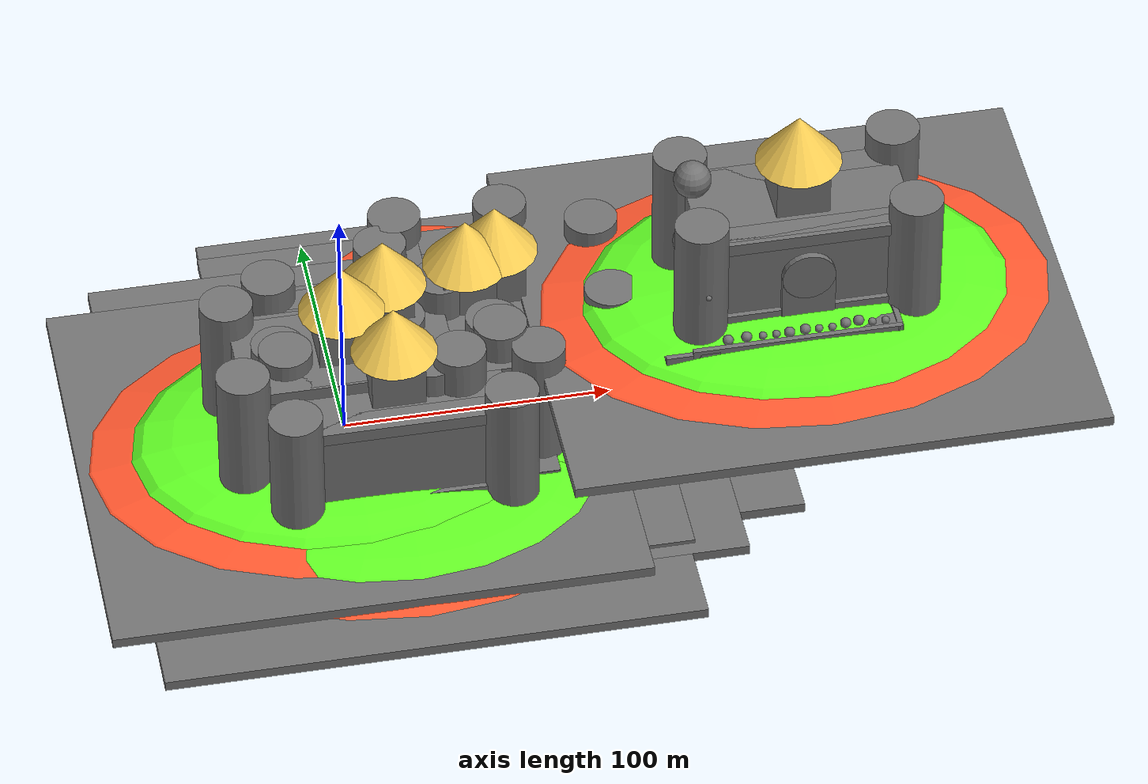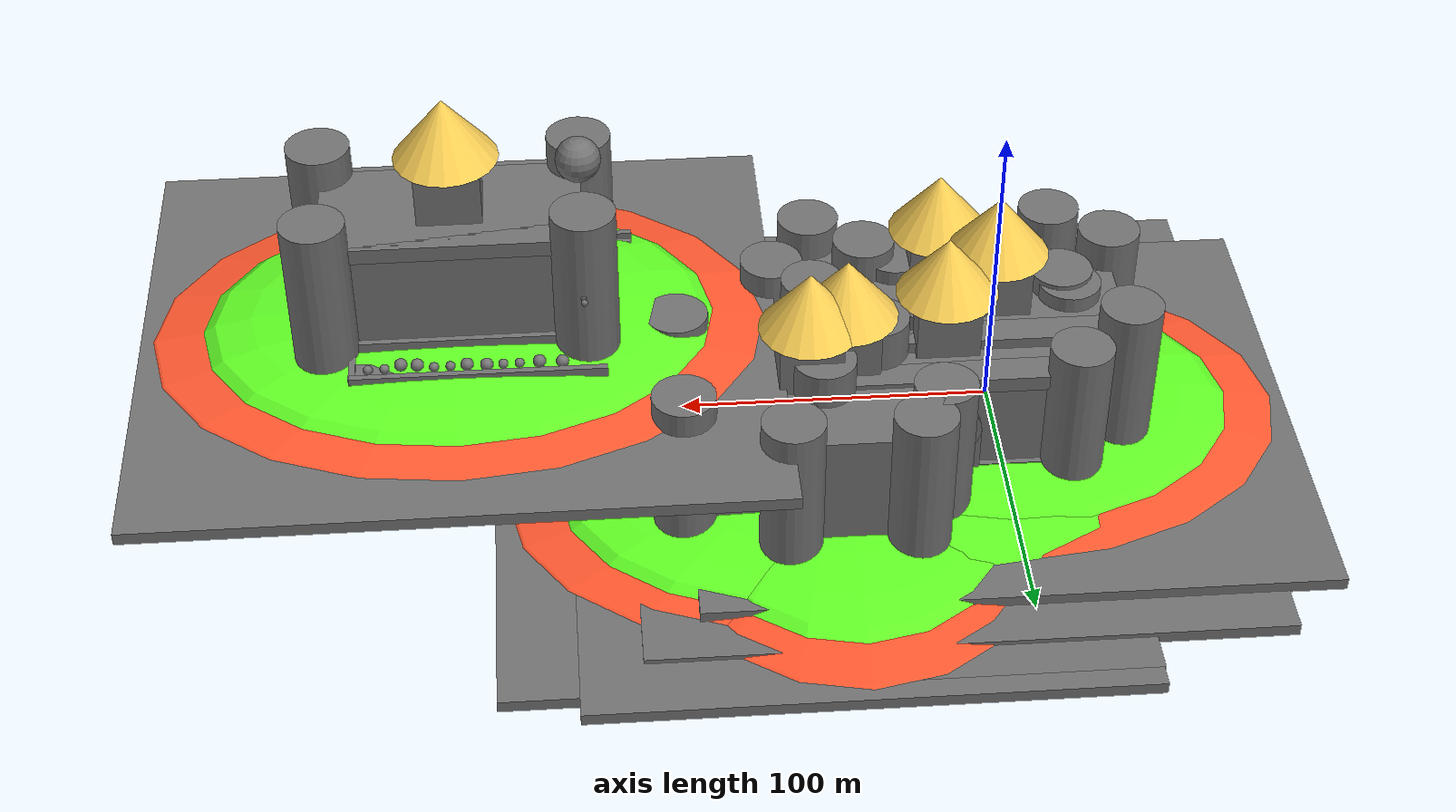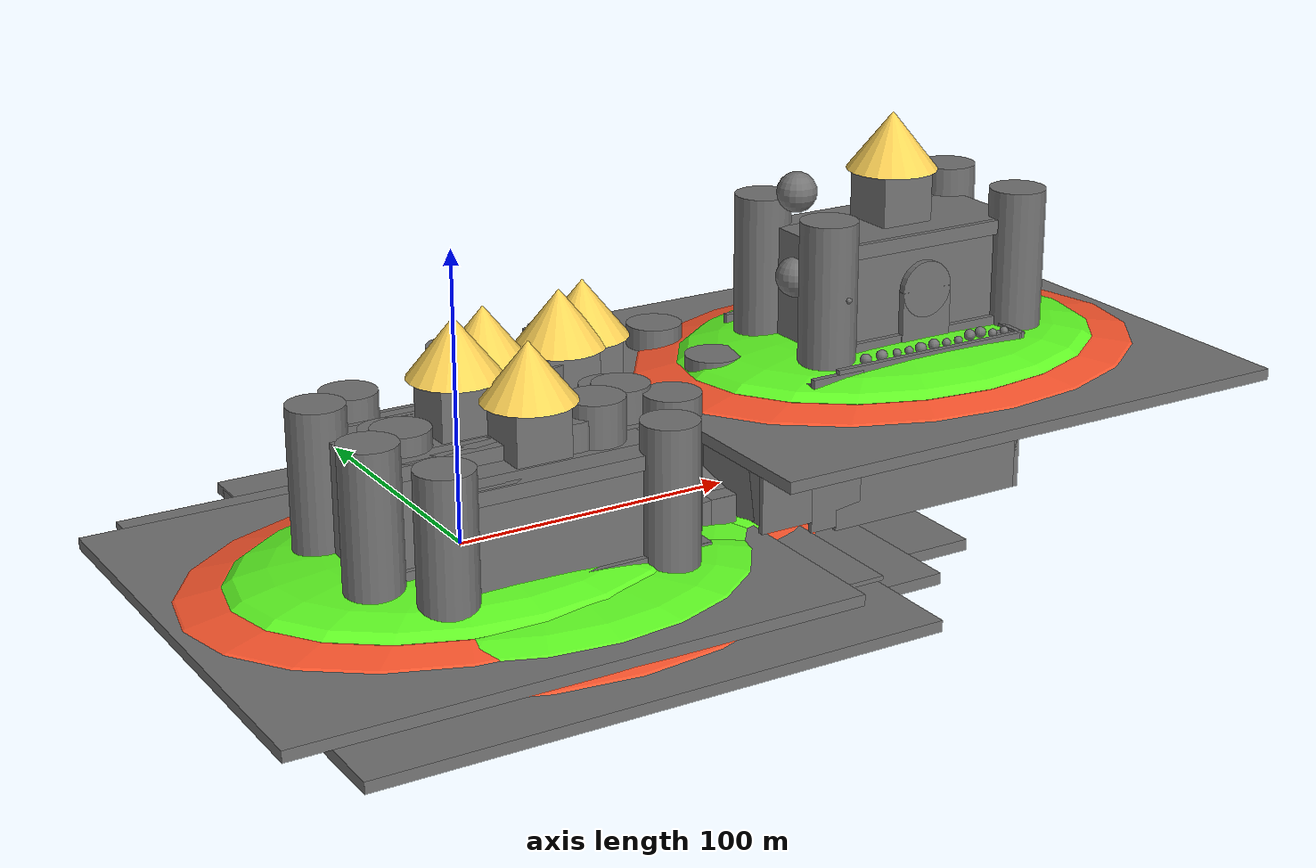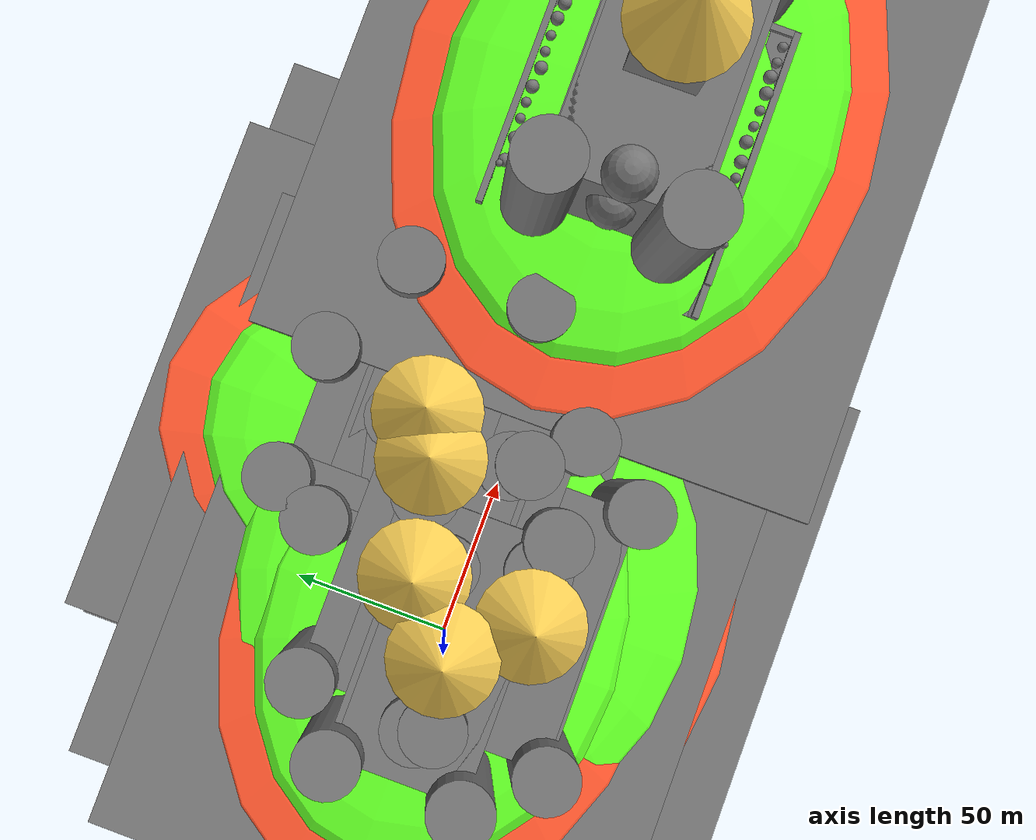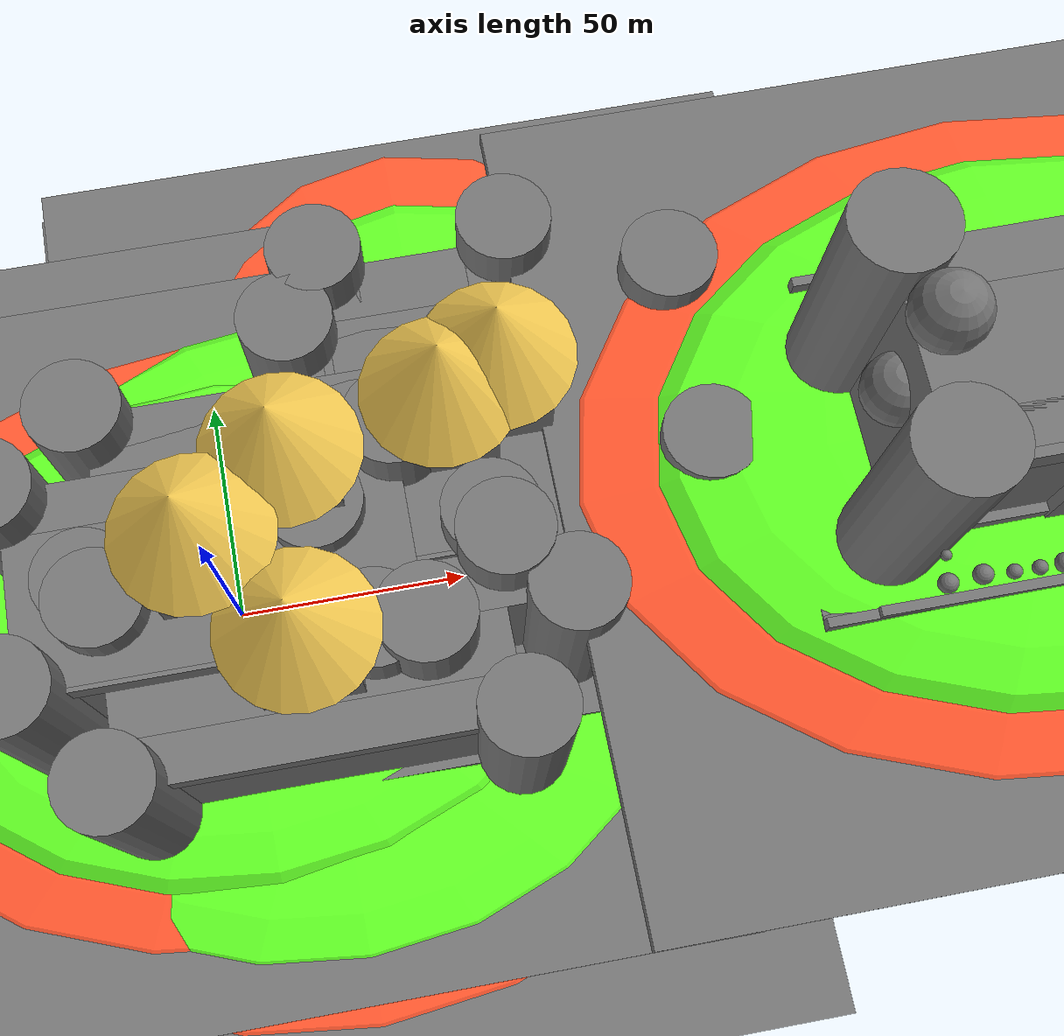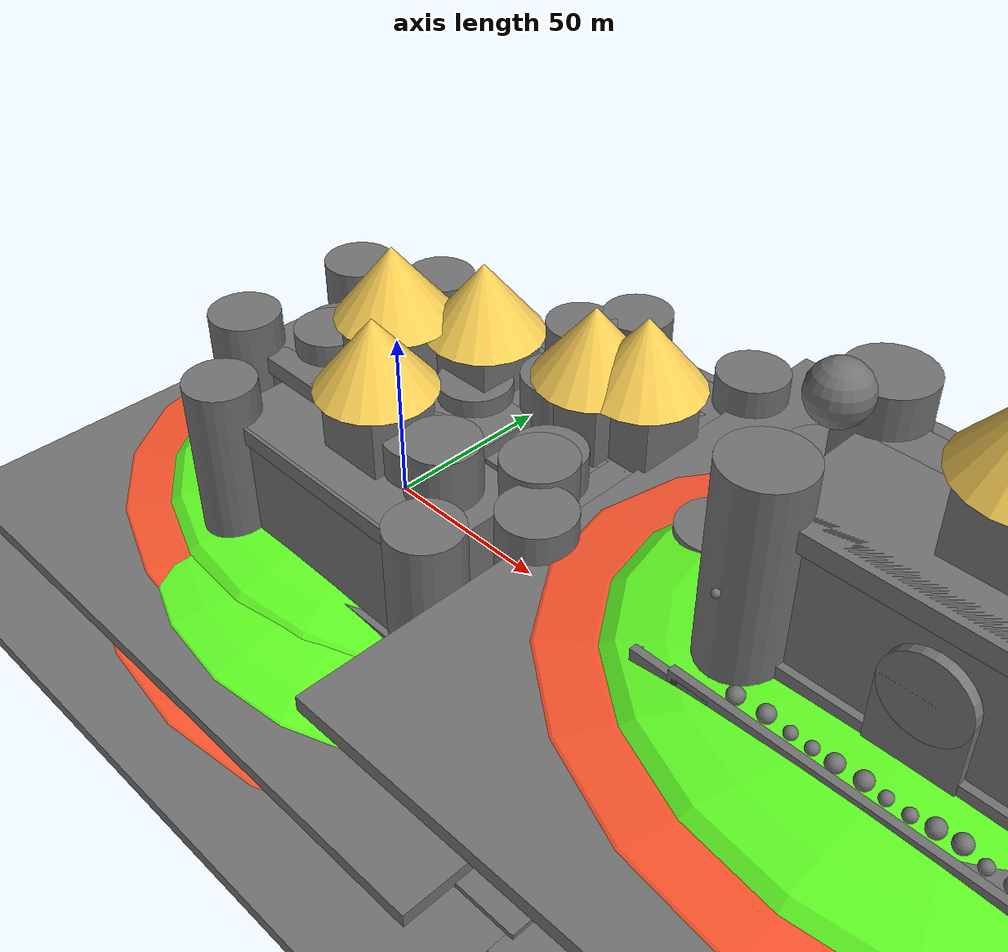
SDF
<sdf version='1.10'>
  <world name='waterworld'>
    <!-- Physics: realistic & consistent on basic machines -->
    <physics name="ode_cpu" type="ode">
      <!-- 500 Hz sim tick; good balance for CPU-only -->
      <max_step_size>0.002</max_step_size>
      <real_time_update_rate>500</real_time_update_rate>
      <real_time_factor>1.0</real_time_factor>
      <ode>
        <solver>
          <type>quick</type>
          <iters>50</iters>
          <sor>1.3</sor>
        </solver>
        <!-- Contact params tuned for stable, non-bouncy flips -->
        <constraints>
          <cfm>0.0</cfm>
          <erp>0.2</erp>
        </constraints>
      </ode>
    </physics>

    <plugin name='gz::sim::systems::Physics' filename='gz-sim-physics-system'/>
    <plugin name='gz::sim::systems::UserCommands' filename='gz-sim-user-commands-system'/>
    <plugin name='gz::sim::systems::SceneBroadcaster' filename='gz-sim-scene-broadcaster-system'/>
    <plugin name='gz::sim::systems::Contact' filename='gz-sim-contact-system'/>
    <plugin filename="gz-sim-sensors-system" name="gz::sim::systems::Sensors"><render_engine>ogre2</render_engine></plugin>

     <!-- Earth gravity -->
    <gravity>0 0 -9.81</gravity>

    <magnetic_field>5.5644999999999998e-06 2.2875799999999999e-05 -4.2388400000000002e-05</magnetic_field>
    <atmosphere type='adiabatic'/>

    <!-- Lighting: simple, stable; shadows off by default -->
    <scene>
      <ambient>0.5 0.5 0.5 1</ambient>
      <background>0.7 0.7 0.75 1</background>
      <shadows>false</shadows>
    </scene>

    <model name="central_tower">
      <static>true</static>
      <link name="link">
        <pose>0 0 0 0 0 0</pose>
        <collision name="col"><geometry><box><size>8 8 10</size></box></geometry></collision>
        <visual name="vis">
          <geometry><box><size>8 8 10</size></box></geometry>
          <material>
            <ambient>0.35 0.35 0.35 1</ambient>
            <diffuse>0.45 0.45 0.45 1</diffuse>
            <!-- This tag and its contents add texture (an image) to our models -->
            <pbr>
              <metal>
                <!-- Point to your image -->
                <albedo_map>model://textures/stone_textures/stone_wall_seamless_1x1.jpg</albedo_map>
                <!-- Optional: roughness/metalness for a matte, non-metal look -->
                <roughness>0.9</roughness>
                <metalness>0.0</metalness>
              </metal>
            </pbr>
          </material>
        </visual>
      </link>
    </model>

    <!-- floor with realistic surface params -->
    <model name="central_arena_floor_model">
      <static>true</static>
      <pose>0 0 5 0 0 0</pose>
      <link name="central_arena_floor_link">
        <collision name="col">
          <geometry><box><size>8 8 0.1</size></box></geometry>
          <surface>
            <!-- Rubber-ish tires on painted plywood/concrete -->
            <friction>
              <ode>
                <mu>0.9</mu>
                <mu2>0.9</mu2>
                <fdir1>1 0 0</fdir1>
              </ode>
            </friction>
            <bounce>
              <restitution_coefficient>0.03</restitution_coefficient>
              <threshold>1e3</threshold>
            </bounce>
            <contact>
              <ode>
                <kp>1e6</kp>
                <kd>1e3</kd>
                <max_vel>1.0</max_vel>
                <min_depth>0.001</min_depth>
              </ode>
            </contact>
          </surface>
        </collision>
        <visual name="vis">
          <geometry><box><size>8 8 0.1</size></box></geometry>
          <material>
            <ambient>0.35 0.35 0.35 1</ambient>
            <diffuse>0.45 0.45 0.45 1</diffuse>
            <!-- This tag and its contents add texture (an image) to our models -->
            <pbr>
              <metal>
                <!-- Point to your image -->
                <albedo_map>model://textures/grass_textures/green_grass_seamless.jpg</albedo_map>
                <!-- Optional: roughness/metalness for a matte, non-metal look -->
                <roughness>0.9</roughness>
                <metalness>0.0</metalness>
              </metal>
            </pbr>
          </material>
        </visual>
      </link>
    </model>

    <model name="west_tower">
      <static>true</static>
      <link name="link">
        <pose>0 12 0 0 0 0</pose>
        <collision name="col"><geometry><box><size>8 8 10</size></box></geometry></collision>
        <visual name="vis">
          <geometry><box><size>8 8 10</size></box></geometry>
          <material>
            <ambient>0.35 0.35 0.35 1</ambient>
            <diffuse>0.45 0.45 0.45 1</diffuse>
            <!-- This tag and its contents add texture (an image) to our models -->
            <pbr>
              <metal>
                <!-- Point to your image -->
                <albedo_map>model://textures/stone_textures/stone_wall_seamless_1x1.jpg</albedo_map>
                <!-- Optional: roughness/metalness for a matte, non-metal look -->
                <roughness>0.9</roughness>
                <metalness>0.0</metalness>
              </metal>
            </pbr>
          </material>
        </visual>
      </link>
    </model>

    <!-- floor with realistic surface params -->
    <model name="west_arena_floor_model">
      <static>true</static>
      <pose>0 12 5 0 0 0</pose>
      <link name="west_arena_floor_link">
        <collision name="col">
          <geometry><box><size>8 8 0.1</size></box></geometry>
          <surface>
            <!-- Rubber-ish tires on painted plywood/concrete -->
            <friction>
              <ode>
                <mu>0.9</mu>
                <mu2>0.9</mu2>
                <fdir1>1 0 0</fdir1>
              </ode>
            </friction>
            <bounce>
              <restitution_coefficient>0.03</restitution_coefficient>
              <threshold>1e3</threshold>
            </bounce>
            <contact>
              <ode>
                <kp>1e6</kp>
                <kd>1e3</kd>
                <max_vel>1.0</max_vel>
                <min_depth>0.001</min_depth>
              </ode>
            </contact>
          </surface>
        </collision>
        <visual name="vis">
          <geometry><box><size>8 8 0.1</size></box></geometry>
          <material>
            <ambient>0.35 0.35 0.35 1</ambient>
            <diffuse>0.45 0.45 0.45 1</diffuse>
            <!-- This tag and its contents add texture (an image) to our models -->
            <pbr>
              <metal>
                <!-- Point to your image -->
                <albedo_map>model://textures/grass_textures/green_grass_seamless.jpg</albedo_map>
                <!-- Optional: roughness/metalness for a matte, non-metal look -->
                <roughness>0.9</roughness>
                <metalness>0.0</metalness>
              </metal>
            </pbr>
          </material>
        </visual>
      </link>
    </model>

    <model name="east_tower">
      <static>true</static>
      <link name="link">
        <pose>0 -12 0 0 0 0</pose>
        <collision name="col"><geometry><box><size>8 8 10</size></box></geometry></collision>
        <visual name="vis">
          <geometry><box><size>8 8 10</size></box></geometry>
          <material>
            <ambient>0.35 0.35 0.35 1</ambient>
            <diffuse>0.45 0.45 0.45 1</diffuse>
            <!-- This tag and its contents add texture (an image) to our models -->
            <pbr>
              <metal>
                <!-- Point to your image -->
                <albedo_map>model://textures/stone_textures/stone_wall_seamless_1x1.jpg</albedo_map>
                <!-- Optional: roughness/metalness for a matte, non-metal look -->
                <roughness>0.9</roughness>
                <metalness>0.0</metalness>
              </metal>
            </pbr>
          </material>
        </visual>
      </link>
    </model>

    <!-- floor with realistic surface params -->
    <model name="east_arena_floor_model">
      <static>true</static>
      <pose>0 -12 5 0 0 0</pose>
      <link name="east_arena_floor_link">
        <collision name="col">
          <geometry><box><size>8 8 0.1</size></box></geometry>
          <surface>
            <!-- Rubber-ish tires on painted plywood/concrete -->
            <friction>
              <ode>
                <mu>0.9</mu>
                <mu2>0.9</mu2>
                <fdir1>1 0 0</fdir1>
              </ode>
            </friction>
            <bounce>
              <restitution_coefficient>0.03</restitution_coefficient>
              <threshold>1e3</threshold>
            </bounce>
            <contact>
              <ode>
                <kp>1e6</kp>
                <kd>1e3</kd>
                <max_vel>1.0</max_vel>
                <min_depth>0.001</min_depth>
              </ode>
            </contact>
          </surface>
        </collision>
        <visual name="vis">
          <geometry><box><size>8 8 0.1</size></box></geometry>
          <material>
            <ambient>0.35 0.35 0.35 1</ambient>
            <diffuse>0.45 0.45 0.45 1</diffuse>
            <!-- This tag and its contents add texture (an image) to our models -->
            <pbr>
              <metal>
                <!-- Point to your image -->
                <albedo_map>model://textures/grass_textures/green_grass_seamless.jpg</albedo_map>
                <!-- Optional: roughness/metalness for a matte, non-metal look -->
                <roughness>0.9</roughness>
                <metalness>0.0</metalness>
              </metal>
            </pbr>
          </material>
        </visual>
      </link>
    </model>

    <model name="north_tower">
      <static>true</static>
      <link name="link">
        <pose>15 0 0 0 0 0</pose>
        <collision name="col"><geometry><box><size>8 8 10</size></box></geometry></collision>
        <visual name="vis">
          <geometry><box><size>8 8 10</size></box></geometry>
          <material>
            <ambient>0.35 0.35 0.35 1</ambient>
            <diffuse>0.45 0.45 0.45 1</diffuse>
            <!-- This tag and its contents add texture (an image) to our models -->
            <pbr>
              <metal>
                <!-- Point to your image -->
                <albedo_map>model://textures/stone_textures/stone_wall_seamless_1x1.jpg</albedo_map>
                <!-- Optional: roughness/metalness for a matte, non-metal look -->
                <roughness>0.9</roughness>
                <metalness>0.0</metalness>
              </metal>
            </pbr>
          </material>
        </visual>
      </link>
    </model>

    <!-- floor with realistic surface params -->
    <model name="north_arena_floor_model">
      <static>true</static>
      <pose>15 0 5 0 0 0</pose>
      <link name="north_arena_floor_link">
        <collision name="col">
          <geometry><box><size>8 8 0.1</size></box></geometry>
          <surface>
            <!-- Rubber-ish tires on painted plywood/concrete -->
            <friction>
              <ode>
                <mu>0.9</mu>
                <mu2>0.9</mu2>
                <fdir1>1 0 0</fdir1>
              </ode>
            </friction>
            <bounce>
              <restitution_coefficient>0.03</restitution_coefficient>
              <threshold>1e3</threshold>
            </bounce>
            <contact>
              <ode>
                <kp>1e6</kp>
                <kd>1e3</kd>
                <max_vel>1.0</max_vel>
                <min_depth>0.001</min_depth>
              </ode>
            </contact>
          </surface>
        </collision>
        <visual name="vis">
          <geometry><box><size>8 8 0.1</size></box></geometry>
          <material>
            <ambient>0.35 0.35 0.35 1</ambient>
            <diffuse>0.45 0.45 0.45 1</diffuse>
            <!-- This tag and its contents add texture (an image) to our models -->
            <pbr>
              <metal>
                <!-- Point to your image -->
                <albedo_map>model://textures/grass_textures/green_grass_seamless.jpg</albedo_map>
                <!-- Optional: roughness/metalness for a matte, non-metal look -->
                <roughness>0.9</roughness>
                <metalness>0.0</metalness>
              </metal>
            </pbr>
          </material>
        </visual>
      </link>
    </model>

    <model name="tidal_island_segment_1">
      <static>true</static>
      <link name="link">
        <pose>35 -8 -2.2 0 0 0</pose>
        <collision name="col"><geometry><box><size>8 24 6</size></box></geometry></collision>
        <visual name="vis">
          <geometry><box><size>8 24 6</size></box></geometry>
          <material>
            <ambient>0.35 0.35 0.35 1</ambient>
            <diffuse>0.45 0.45 0.45 1</diffuse>
            <!-- This tag and its contents add texture (an image) to our models -->
            <pbr>
              <metal>
                <!-- Point to your image -->
                <albedo_map>model://textures/stone_textures/stone_wall_seamless_1x1.jpg</albedo_map>
                <!-- Optional: roughness/metalness for a matte, non-metal look -->
                <roughness>0.9</roughness>
                <metalness>0.0</metalness>
              </metal>
            </pbr>
          </material>
        </visual>
      </link>
    </model>

    <model name="tidal_island_segment_1_ramp">
      <static>true</static>
      <link name="link">
        <pose>33 -8 -0.1 0 0.4 0</pose>
        <collision name="col"><geometry><box><size>3 10 3</size></box></geometry></collision>
        <visual name="vis">
          <geometry><box><size>3 10 3</size></box></geometry>
          <material>
            <ambient>0.35 0.35 0.35 1</ambient>
            <diffuse>0.45 0.45 0.45 1</diffuse>
            <!-- This tag and its contents add texture (an image) to our models -->
            <pbr>
              <metal>
                <!-- Point to your image -->
                <albedo_map>model://textures/stone_textures/stone_wall_seamless_1x1.jpg</albedo_map>
                <!-- Optional: roughness/metalness for a matte, non-metal look -->
                <roughness>0.9</roughness>
                <metalness>0.0</metalness>
              </metal>
            </pbr>
          </material>
        </visual>
      </link>
    </model>

    <!-- floor with realistic surface params -->
    <model name="tidal_island_segment_1_floor_model">
      <static>true</static>
      <pose>35 -8 0.8 0 0 0</pose>
      <link name="north_arena_floor_link">
        <collision name="col">
          <geometry><box><size>8 24 0.1</size></box></geometry>
          <surface>
            <!-- Rubber-ish tires on painted plywood/concrete -->
            <friction>
              <ode>
                <mu>0.9</mu>
                <mu2>0.9</mu2>
                <fdir1>1 0 0</fdir1>
              </ode>
            </friction>
            <bounce>
              <restitution_coefficient>0.03</restitution_coefficient>
              <threshold>1e3</threshold>
            </bounce>
            <contact>
              <ode>
                <kp>1e6</kp>
                <kd>1e3</kd>
                <max_vel>1.0</max_vel>
                <min_depth>0.001</min_depth>
              </ode>
            </contact>
          </surface>
        </collision>
        <visual name="vis">
          <geometry><box><size>8 24 0.1</size></box></geometry>
          <material>
            <ambient>0.35 0.35 0.35 1</ambient>
            <diffuse>0.45 0.45 0.45 1</diffuse>
            <!-- This tag and its contents add texture (an image) to our models -->
            <pbr>
              <metal>
                <!-- Point to your image -->
                <albedo_map>model://textures/grass_textures/green_grass_seamless.jpg</albedo_map>
                <!-- Optional: roughness/metalness for a matte, non-metal look -->
                <roughness>0.9</roughness>
                <metalness>0.0</metalness>
              </metal>
            </pbr>
          </material>
        </visual>
      </link>
    </model>

    <model name="tidal_island_segment_2">
      <static>true</static>
      <link name="link">
        <pose>40.3641 -8 -2.4876 0 0.2 0</pose>
        <collision name="col"><geometry><box><size>4 24 6</size></box></geometry></collision>
        <visual name="vis">
          <geometry><box><size>4 24 6</size></box></geometry>
          <material>
            <ambient>0.35 0.35 0.35 1</ambient>
            <diffuse>0.45 0.45 0.45 1</diffuse>
            <!-- This tag and its contents add texture (an image) to our models -->
            <pbr>
              <metal>
                <!-- Point to your image -->
                <albedo_map>model://textures/stone_textures/stone_wall_seamless_4x1.jpg</albedo_map>
                <!-- Optional: roughness/metalness for a matte, non-metal look -->
                <roughness>0.9</roughness>
                <metalness>0.0</metalness>
              </metal>
            </pbr>
          </material>
        </visual>
      </link>
    </model>

    <model name="tidal_island_segment_3">
      <static>true</static>
      <link name="link">
        <pose>44.2 -8 -2.8 0 0 0</pose>
        <collision name="col"><geometry><box><size>5 24 6</size></box></geometry></collision>
        <visual name="vis">
          <geometry><box><size>5 24 6</size></box></geometry>
          <material>
            <ambient>0.35 0.35 0.35 1</ambient>
            <diffuse>0.45 0.45 0.45 1</diffuse>
            <!-- This tag and its contents add texture (an image) to our models -->
            <pbr>
              <metal>
                <!-- Point to your image -->
                <albedo_map>model://textures/stone_textures/stone_wall_seamless_4x1.jpg</albedo_map>
                <!-- Optional: roughness/metalness for a matte, non-metal look -->
                <roughness>0.9</roughness>
                <metalness>0.0</metalness>
              </metal>
            </pbr>
          </material>
        </visual>
      </link>
    </model>

    <model name="tidal_island_segment_4">
      <static>true</static>
      <link name="link">
        <pose>48 -8 -2.4876 0 -0.2 0</pose>
        <collision name="col"><geometry><box><size>4 24 6</size></box></geometry></collision>
        <visual name="vis">
          <geometry><box><size>4 24 6</size></box></geometry>
          <material>
            <ambient>0.35 0.35 0.35 1</ambient>
            <diffuse>0.45 0.45 0.45 1</diffuse>
            <!-- This tag and its contents add texture (an image) to our models -->
            <pbr>
              <metal>
                <!-- Point to your image -->
                <albedo_map>model://textures/stone_textures/stone_wall_seamless_4x1.jpg</albedo_map>
                <!-- Optional: roughness/metalness for a matte, non-metal look -->
                <roughness>0.9</roughness>
                <metalness>0.0</metalness>
              </metal>
            </pbr>
          </material>
        </visual>
      </link>
    </model>

    <model name="tidal_island_segment_5">
      <static>true</static>
      <link name="link">
        <pose>53.3641 -8 -2.2 0 0 0</pose>
        <collision name="col"><geometry><box><size>8 24 6</size></box></geometry></collision>
        <visual name="vis">
          <geometry><box><size>8 24 6</size></box></geometry>
          <material>
            <ambient>0.35 0.35 0.35 1</ambient>
            <diffuse>0.45 0.45 0.45 1</diffuse>
            <!-- This tag and its contents add texture (an image) to our models -->
            <pbr>
              <metal>
                <!-- Point to your image -->
                <albedo_map>model://textures/stone_textures/stone_wall_seamless_1x1.jpg</albedo_map>
                <!-- Optional: roughness/metalness for a matte, non-metal look -->
                <roughness>0.9</roughness>
                <metalness>0.0</metalness>
              </metal>
            </pbr>
          </material>
        </visual>
      </link>
    </model>

    <!-- floor with realistic surface params -->
    <model name="tidal_island_segment_5_floor_model">
      <static>true</static>
      <pose>53.3641 -8 0.7999 0 0 0</pose>
      <link name="north_arena_floor_link">
        <collision name="col">
          <geometry><box><size>8 24 0.1</size></box></geometry>
          <surface>
            <!-- Rubber-ish tires on painted plywood/concrete -->
            <friction>
              <ode>
                <mu>0.9</mu>
                <mu2>0.9</mu2>
                <fdir1>1 0 0</fdir1>
              </ode>
            </friction>
            <bounce>
              <restitution_coefficient>0.03</restitution_coefficient>
              <threshold>1e3</threshold>
            </bounce>
            <contact>
              <ode>
                <kp>1e6</kp>
                <kd>1e3</kd>
                <max_vel>1.0</max_vel>
                <min_depth>0.001</min_depth>
              </ode>
            </contact>
          </surface>
        </collision>
        <visual name="vis">
          <geometry><box><size>8 24 0.1</size></box></geometry>
          <material>
            <ambient>0.35 0.35 0.35 1</ambient>
            <diffuse>0.45 0.45 0.45 1</diffuse>
            <!-- This tag and its contents add texture (an image) to our models -->
            <pbr>
              <metal>
                <!-- Point to your image -->
                <albedo_map>model://textures/grass_textures/green_grass_seamless.jpg</albedo_map>
                <!-- Optional: roughness/metalness for a matte, non-metal look -->
                <roughness>0.9</roughness>
                <metalness>0.0</metalness>
              </metal>
            </pbr>
          </material>
        </visual>
      </link>
    </model>

    <model name="north_bridge">
      <static>true</static>
      <link name="link">
        <pose>7.5 0 4.925 0 0 0</pose>
        <collision name="col">
          <!-- width x length x height -->
          <geometry><box><size>7 3 0.25</size></box></geometry>
        </collision>
        <visual name="vis">
          <geometry><box><size>7 3 0.25</size></box></geometry>
          <material>
            <ambient>0.35 0.35 0.35 1</ambient>
            <diffuse>0.45 0.45 0.45 1</diffuse>
            <!-- This tag and its contents add texture (an image) to our models -->
            <pbr>
              <metal>
                <!-- Point to your image -->
                <albedo_map>model://textures/wood_textures/wood_texture_seamless_1x2.jpg</albedo_map>
                <!-- Optional: roughness/metalness for a matte, non-metal look -->
                <roughness>0.9</roughness>
                <metalness>0.0</metalness>
              </metal>
            </pbr>
          </material>
        </visual>
      </link>
    </model>

    <model name="east_bridge">
      <static>true</static>
      <link name="link">
        <pose>0 -6 4.925 0 0 0</pose>
        <collision name="col">
          <!-- width x length x height -->
          <geometry><box><size>3 4 0.25</size></box></geometry>
        </collision>
        <visual name="vis">
          <geometry><box><size>3 4 0.25</size></box></geometry>
          <material>
            <ambient>0.35 0.35 0.35 1</ambient>
            <diffuse>0.45 0.45 0.45 1</diffuse>
            <!-- This tag and its contents add texture (an image) to our models -->
            <pbr>
              <metal>
                <!-- Point to your image -->
                <albedo_map>model://textures/wood_textures/wood_texture_seamless_1x1.jpg</albedo_map>
                <!-- Optional: roughness/metalness for a matte, non-metal look -->
                <roughness>0.9</roughness>
                <metalness>0.0</metalness>
              </metal>
            </pbr>
          </material>
        </visual>
      </link>
    </model>

    <model name="west_bridge">
      <static>true</static>
      <link name="link">
        <pose>0 6 4.925 0 0 0</pose>
        <collision name="col">
          <!-- width x length x height -->
          <geometry><box><size>3 4 0.25</size></box></geometry>
        </collision>
        <visual name="vis">
          <geometry><box><size>3 4 0.25</size></box></geometry>
          <material>
            <ambient>0.35 0.35 0.35 1</ambient>
            <diffuse>0.45 0.45 0.45 1</diffuse>
            <!-- This tag and its contents add texture (an image) to our models -->
            <pbr>
              <metal>
                <!-- Point to your image -->
                <albedo_map>model://textures/wood_textures/wood_texture_seamless_1x1.jpg</albedo_map>
                <!-- Optional: roughness/metalness for a matte, non-metal look -->
                <roughness>0.9</roughness>
                <metalness>0.0</metalness>
              </metal>
            </pbr>
          </material>
        </visual>
      </link>
    </model>

    <model name="east_north_bridge">
      <static>true</static>
      <link name="link">
        <pose>7.39 -12 4.165 0 0.22 0</pose>
        <collision name="col">
          <!-- width x length x height -->
          <geometry><box><size>7 3 0.25</size></box></geometry>
        </collision>
        <visual name="vis">
          <geometry><box><size>7 3 0.25</size></box></geometry>
          <material>
            <ambient>0.35 0.35 0.35 1</ambient>
            <diffuse>0.45 0.45 0.45 1</diffuse>
            <!-- This tag and its contents add texture (an image) to our models -->
            <pbr>
              <metal>
                <!-- Point to your image -->
                <albedo_map>model://textures/wood_textures/wood_texture_seamless_1x2.jpg</albedo_map>
                <!-- Optional: roughness/metalness for a matte, non-metal look -->
                <roughness>0.9</roughness>
                <metalness>0.0</metalness>
              </metal>
            </pbr>
          </material>
        </visual>
      </link>
    </model>

    <model name="west_north_bridge_platform">
      <static>true</static>
      <link name="link">
        <pose>2.5 18 4.925 0 0 0</pose>
        <collision name="col">
          <!-- width x length x height -->
          <geometry><box><size>3 4 0.25</size></box></geometry>
        </collision>
        <visual name="vis">
          <geometry><box><size>3 4 0.25</size></box></geometry>
          <material>
            <ambient>0.35 0.35 0.35 1</ambient>
            <diffuse>0.45 0.45 0.45 1</diffuse>
            <!-- This tag and its contents add texture (an image) to our models -->
            <pbr>
              <metal>
                <!-- Point to your image -->
                <albedo_map>model://textures/wood_textures/wood_texture_seamless_1x1.jpg</albedo_map>
                <!-- Optional: roughness/metalness for a matte, non-metal look -->
                <roughness>0.9</roughness>
                <metalness>0.0</metalness>
              </metal>
            </pbr>
          </material>
        </visual>
      </link>
    </model>

    <model name="west_north_bridge">
      <static>true</static>
      <link name="link">
        <pose>8.328 18 2.543 0 0.5 0</pose>
        <collision name="col">
          <!-- width x length x height -->
          <geometry><box><size>10 4 0.25</size></box></geometry>
        </collision>
        <visual name="vis">
          <geometry><box><size>10 4 0.25</size></box></geometry>
          <material>
            <ambient>0.35 0.35 0.35 1</ambient>
            <diffuse>0.45 0.45 0.45 1</diffuse>
            <!-- This tag and its contents add texture (an image) to our models -->
            <pbr>
              <metal>
                <!-- Point to your image -->
                <albedo_map>model://textures/wood_textures/wood_texture_seamless_1x3.jpg</albedo_map>
                <!-- Optional: roughness/metalness for a matte, non-metal look -->
                <roughness>0.9</roughness>
                <metalness>0.0</metalness>
              </metal>
            </pbr>
          </material>
        </visual>
      </link>
    </model>

    <model name="west_north_north_bridge">
      <static>true</static>
      <link name="link">
        <pose>31 12.2 2.5 0 -0.2 0</pose>
        <collision name="col">
          <!-- width x length x height -->
          <geometry><box><size>25 3 0.25</size></box></geometry>
        </collision>
        <visual name="vis">
          <geometry><box><size>25 3 0.25</size></box></geometry>
          <material>
            <ambient>0.35 0.35 0.35 1</ambient>
            <diffuse>0.45 0.45 0.45 1</diffuse>
            <!-- This tag and its contents add texture (an image) to our models -->
            <pbr>
              <metal>
                <!-- Point to your image -->
                <albedo_map>model://textures/wood_textures/wood_texture_seamless_1x10.jpg</albedo_map>
                <!-- Optional: roughness/metalness for a matte, non-metal look -->
                <roughness>0.9</roughness>
                <metalness>0.0</metalness>
              </metal>
            </pbr>
          </material>
        </visual>
      </link>
    </model>

    <model name="north_north_bridge_platform_1">
      <static>true</static>
      <link name="link">
        <pose>17.5 6 4.925 0 0 0</pose>
        <collision name="col">
          <!-- width x length x height -->
          <geometry><box><size>3 4 0.25</size></box></geometry>
        </collision>
        <visual name="vis">
          <geometry><box><size>3 4 0.25</size></box></geometry>
          <material>
            <ambient>0.35 0.35 0.35 1</ambient>
            <diffuse>0.45 0.45 0.45 1</diffuse>
            <!-- This tag and its contents add texture (an image) to our models -->
            <pbr>
              <metal>
                <!-- Point to your image -->
                <albedo_map>model://textures/wood_textures/wood_texture_seamless_1x3.jpg</albedo_map>
                <!-- Optional: roughness/metalness for a matte, non-metal look -->
                <roughness>0.9</roughness>
                <metalness>0.0</metalness>
              </metal>
            </pbr>
          </material>
        </visual>
      </link>
    </model>

    <model name="north_north_bridge">
      <static>true</static>
      <link name="link">
        <pose>25.1 6 2.82 0 0.33 0</pose>
        <collision name="col">
          <!-- width x length x height -->
          <geometry><box><size>13 4 0.25</size></box></geometry>
        </collision>
        <visual name="vis">
          <geometry><box><size>13 4 0.25</size></box></geometry>
          <material>
            <ambient>0.35 0.35 0.35 1</ambient>
            <diffuse>0.45 0.45 0.45 1</diffuse>
            <!-- This tag and its contents add texture (an image) to our models -->
            <pbr>
              <metal>
                <!-- Point to your image -->
                <albedo_map>model://textures/wood_textures/wood_texture_seamless_1x3.jpg</albedo_map>
                <!-- Optional: roughness/metalness for a matte, non-metal look -->
                <roughness>0.9</roughness>
                <metalness>0.0</metalness>
              </metal>
            </pbr>
          </material>
        </visual>
      </link>
    </model>

    <model name="north_north_bridge_platform_2">
      <static>true</static>
      <link name="link">
        <pose>32.5 6 0.725 0 0 0</pose>
        <collision name="col">
          <!-- width x length x height -->
          <geometry><box><size>3 4 0.25</size></box></geometry>
        </collision>
        <visual name="vis">
          <geometry><box><size>3 4 0.25</size></box></geometry>
          <material>
            <ambient>0.35 0.35 0.35 1</ambient>
            <diffuse>0.45 0.45 0.45 1</diffuse>
            <!-- This tag and its contents add texture (an image) to our models -->
            <pbr>
              <metal>
                <!-- Point to your image -->
                <albedo_map>model://textures/wood_textures/wood_texture_seamless_1x1.jpg</albedo_map>
                <!-- Optional: roughness/metalness for a matte, non-metal look -->
                <roughness>0.9</roughness>
                <metalness>0.0</metalness>
              </metal>
            </pbr>
          </material>
        </visual>
      </link>
    </model>

    <model name="east_north_north_bridge">
      <static>true</static>
      <link name="link">
        <pose>27.26 -16 1.986 0 0.3 0</pose>
        <collision name="col">
          <!-- width x length x height -->
          <geometry><box><size>10 4 0.25</size></box></geometry>
        </collision>
        <visual name="vis">
          <geometry><box><size>10 4 0.25</size></box></geometry>
          <material>
            <ambient>0.35 0.35 0.35 1</ambient>
            <diffuse>0.45 0.45 0.45 1</diffuse>
            <!-- This tag and its contents add texture (an image) to our models -->
            <pbr>
              <metal>
                <!-- Point to your image -->
                <albedo_map>model://textures/wood_textures/wood_texture_seamless_1x5.jpg</albedo_map>
                <!-- Optional: roughness/metalness for a matte, non-metal look -->
                <roughness>0.9</roughness>
                <metalness>0.0</metalness>
              </metal>
            </pbr>
          </material>
        </visual>
      </link>
    </model>

    <model name="stone_bridge_1">
      <static>true</static>
      <link name="link">
        <pose>70 -15.999 -2.66 0 -0.12 0</pose>
        <collision name="col"><geometry><box><size>30 8 10</size></box></geometry></collision>
        <visual name="vis">
          <geometry><box><size>30 8 10</size></box></geometry>
          <material>
            <ambient>0.35 0.35 0.35 1</ambient>
            <diffuse>0.45 0.45 0.45 1</diffuse>
            <!-- This tag and its contents add texture (an image) to our models -->
            <pbr>
              <metal>
                <!-- Point to your image -->
                <albedo_map>model://textures/stone_textures/stone_wall_seamless_1x3.jpg</albedo_map>
                <!-- Optional: roughness/metalness for a matte, non-metal look -->
                <roughness>0.9</roughness>
                <metalness>0.0</metalness>
              </metal>
            </pbr>
          </material>
        </visual>
      </link>
    </model>

    <model name="east_north_north_north_bridge_1">
      <static>true</static>
      <link name="link">
        <pose>57.978 14 7.6 0 -0.133 0</pose>
        <collision name="col">
          <!-- width x length x height -->
          <geometry><box><size>19.25 3 0.25</size></box></geometry>
        </collision>
        <visual name="vis">
          <geometry><box><size>19.25 3 0.25</size></box></geometry>
          <material>
            <ambient>0.35 0.35 0.35 1</ambient>
            <diffuse>0.45 0.45 0.45 1</diffuse>
            <!-- This tag and its contents add texture (an image) to our models -->
            <pbr>
              <metal>
                <!-- Point to your image -->
                <albedo_map>model://textures/wood_textures/wood_texture_seamless_1x5.jpg</albedo_map>
                <!-- Optional: roughness/metalness for a matte, non-metal look -->
                <roughness>0.9</roughness>
                <metalness>0.0</metalness>
              </metal>
            </pbr>
          </material>
        </visual>
      </link>
    </model>

    <model name="east_north_north_north_bridge_platform_1">
      <static>true</static>
      <link name="link">
        <pose>70 14 2 0 0 0</pose>
        <collision name="col"><geometry><box><size>5 5 14</size></box></geometry></collision>
        <visual name="vis">
          <geometry><box><size>5 5 14</size></box></geometry>
          <material>
            <ambient>0.35 0.35 0.35 1</ambient>
            <diffuse>0.45 0.45 0.45 1</diffuse>
            <!-- This tag and its contents add texture (an image) to our models -->
            <pbr>
              <metal>
                <!-- Point to your image -->
                <albedo_map>model://textures/stone_textures/stone_wall_seamless_1x1.jpg</albedo_map>
                <!-- Optional: roughness/metalness for a matte, non-metal look -->
                <roughness>0.9</roughness>
                <metalness>0.0</metalness>
              </metal>
            </pbr>
          </material>
        </visual>
      </link>
    </model>

    <model name="east_north_north_north_bridge_2">
      <static>true</static>
      <link name="link">
        <pose>70 22 8.875 0 0 0</pose>
        <collision name="col">
          <!-- width x length x height -->
          <geometry><box><size>3 11 0.25</size></box></geometry>
        </collision>
        <visual name="vis">
          <geometry><box><size>3 11 0.25</size></box></geometry>
          <material>
            <ambient>0.35 0.35 0.35 1</ambient>
            <diffuse>0.45 0.45 0.45 1</diffuse>
            <!-- This tag and its contents add texture (an image) to our models -->
            <pbr>
              <metal>
                <!-- Point to your image -->
                <albedo_map>model://textures/wood_textures/wood_texture_seamless_1x1.jpg</albedo_map>
                <!-- Optional: roughness/metalness for a matte, non-metal look -->
                <roughness>0.9</roughness>
                <metalness>0.0</metalness>
              </metal>
            </pbr>
          </material>
        </visual>
      </link>
    </model>

    <model name="east_north_north_north_bridge_platform_2">
      <static>true</static>
      <link name="link">
        <pose>70 30 2 0 0 0</pose>
        <collision name="col"><geometry><box><size>5 5 14</size></box></geometry></collision>
        <visual name="vis">
          <geometry><box><size>5 5 14</size></box></geometry>
          <material>
            <ambient>0.35 0.35 0.35 1</ambient>
            <diffuse>0.45 0.45 0.45 1</diffuse>
            <!-- This tag and its contents add texture (an image) to our models -->
            <pbr>
              <metal>
                <!-- Point to your image -->
                <albedo_map>model://textures/stone_textures/stone_wall_seamless_1x1.jpg</albedo_map>
                <!-- Optional: roughness/metalness for a matte, non-metal look -->
                <roughness>0.9</roughness>
                <metalness>0.0</metalness>
              </metal>
            </pbr>
          </material>
        </visual>
      </link>
    </model>

    <model name="east_north_north_north_bridge_3">
      <static>true</static>
      <link name="link">
        <pose>78.265 30 10.385 0 -0.25 0</pose>
        <collision name="col">
          <!-- width x length x height -->
          <geometry><box><size>12.5 3 0.25</size></box></geometry>
        </collision>
        <visual name="vis">
          <geometry><box><size>12.5 3 0.25</size></box></geometry>
          <material>
            <ambient>0.35 0.35 0.35 1</ambient>
            <diffuse>0.45 0.45 0.45 1</diffuse>
            <!-- This tag and its contents add texture (an image) to our models -->
            <pbr>
              <metal>
                <!-- Point to your image -->
                <albedo_map>model://textures/wood_textures/wood_texture_seamless_1x5.jpg</albedo_map>
                <!-- Optional: roughness/metalness for a matte, non-metal look -->
                <roughness>0.9</roughness>
                <metalness>0.0</metalness>
              </metal>
            </pbr>
          </material>
        </visual>
      </link>
    </model>

    <model name="ramp_tower_left_landing_1">
      <static>true</static>
      <link name="link">
        <pose>94.29 30 3.5 0 0 0</pose>
        <collision name="col"><geometry><box><size>20 8 17</size></box></geometry></collision>
        <visual name="vis">
          <geometry><box><size>20 8 17</size></box></geometry>
          <material>
            <ambient>0.35 0.35 0.35 1</ambient>
            <diffuse>0.45 0.45 0.45 1</diffuse>
            <!-- This tag and its contents add texture (an image) to our models -->
            <pbr>
              <metal>
                <!-- Point to your image -->
                <albedo_map>model://textures/stone_textures/stone_wall_seamless_1x1.jpg</albedo_map>
                <!-- Optional: roughness/metalness for a matte, non-metal look -->
                <roughness>0.9</roughness>
                <metalness>0.0</metalness>
              </metal>
            </pbr>
          </material>
        </visual>
      </link>
    </model>

    <!-- floor with realistic surface params -->
    <model name="ramp_tower_left_landing_1_floor">
      <static>true</static>
      <pose>94.29 30 12 0 0 0</pose>
      <link name="west_arena_floor_link">
        <collision name="col">
          <geometry><box><size>20 8 0.1</size></box></geometry>
          <surface>
            <!-- Rubber-ish tires on painted plywood/concrete -->
            <friction>
              <ode>
                <mu>0.9</mu>
                <mu2>0.9</mu2>
                <fdir1>1 0 0</fdir1>
              </ode>
            </friction>
            <bounce>
              <restitution_coefficient>0.03</restitution_coefficient>
              <threshold>1e3</threshold>
            </bounce>
            <contact>
              <ode>
                <kp>1e6</kp>
                <kd>1e3</kd>
                <max_vel>1.0</max_vel>
                <min_depth>0.001</min_depth>
              </ode>
            </contact>
          </surface>
        </collision>
        <visual name="vis">
          <geometry><box><size>20 8 0.1</size></box></geometry>
          <material>
            <ambient>0.35 0.35 0.35 1</ambient>
            <diffuse>0.45 0.45 0.45 1</diffuse>
            <!-- This tag and its contents add texture (an image) to our models -->
            <pbr>
              <metal>
                <!-- Point to your image -->
                <albedo_map>model://textures/grass_textures/green_grass_seamless.jpg</albedo_map>
                <!-- Optional: roughness/metalness for a matte, non-metal look -->
                <roughness>0.9</roughness>
                <metalness>0.0</metalness>
              </metal>
            </pbr>
          </material>
        </visual>
      </link>
    </model>

    <model name="ramp_tower_left_landing_1_wall">
      <static>true</static>
      <link name="link">
        <pose>94.29 35 3.5 0 0 0</pose>
        <collision name="col"><geometry><box><size>20 2 22</size></box></geometry></collision>
        <visual name="vis">
          <geometry><box><size>20 2 22</size></box></geometry>
          <material>
            <ambient>0.35 0.35 0.35 1</ambient>
            <diffuse>0.45 0.45 0.45 1</diffuse>
            <!-- This tag and its contents add texture (an image) to our models -->
            <pbr>
              <metal>
                <!-- Point to your image -->
                <albedo_map>model://textures/stone_textures/stone_wall_seamless_1x1.jpg</albedo_map>
                <!-- Optional: roughness/metalness for a matte, non-metal look -->
                <roughness>0.9</roughness>
                <metalness>0.0</metalness>
              </metal>
            </pbr>
          </material>
        </visual>
      </link>
    </model>

    <model name="ramp_tower_left_landing_1_ramp">
      <static>true</static>
      <link name="link">
        <pose>94.6 33 11 0.40 -0.05 0</pose>
        <collision name="col"><geometry><box><size>20.4 5 3</size></box></geometry></collision>
        <visual name="vis">
          <geometry><box><size>20.4 5 3</size></box></geometry>
          <material>
            <ambient>0.35 0.35 0.35 1</ambient>
            <diffuse>0.45 0.45 0.45 1</diffuse>
            <!-- This tag and its contents add texture (an image) to our models -->
            <pbr>
              <metal>
                <!-- Point to your image -->
                <albedo_map>model://textures/stone_textures/stone_wall_seamless_1x1.jpg</albedo_map>
                <!-- Optional: roughness/metalness for a matte, non-metal look -->
                <roughness>0.9</roughness>
                <metalness>0.0</metalness>
              </metal>
            </pbr>
          </material>
        </visual>
      </link>
    </model>

    <model name="ramp_tower_right_landing_1">
      <static>true</static>
      <link name="link">
        <pose>89.29 -15.999 -0.95 0 0 0</pose>
        <collision name="col"><geometry><box><size>10 8 10</size></box></geometry></collision>
        <visual name="vis">
          <geometry><box><size>10 8 10</size></box></geometry>
          <material>
            <ambient>0.35 0.35 0.35 1</ambient>
            <diffuse>0.45 0.45 0.45 1</diffuse>
            <!-- This tag and its contents add texture (an image) to our models -->
            <pbr>
              <metal>
                <!-- Point to your image -->
                <albedo_map>model://textures/stone_textures/stone_wall_seamless_1x1.jpg</albedo_map>
                <!-- Optional: roughness/metalness for a matte, non-metal look -->
                <roughness>0.9</roughness>
                <metalness>0.0</metalness>
              </metal>
            </pbr>
          </material>
        </visual>
      </link>
    </model>

    <!-- floor with realistic surface params -->
    <model name="ramp_tower_right_landing_1_floor">
      <static>true</static>
      <pose>89.29 -15.999 4.05 0 0 0</pose>
      <link name="west_arena_floor_link">
        <collision name="col">
          <geometry><box><size>10 8 0.1</size></box></geometry>
          <surface>
            <!-- Rubber-ish tires on painted plywood/concrete -->
            <friction>
              <ode>
                <mu>0.9</mu>
                <mu2>0.9</mu2>
                <fdir1>1 0 0</fdir1>
              </ode>
            </friction>
            <bounce>
              <restitution_coefficient>0.03</restitution_coefficient>
              <threshold>1e3</threshold>
            </bounce>
            <contact>
              <ode>
                <kp>1e6</kp>
                <kd>1e3</kd>
                <max_vel>1.0</max_vel>
                <min_depth>0.001</min_depth>
              </ode>
            </contact>
          </surface>
        </collision>
        <visual name="vis">
          <geometry><box><size>10 8 0.1</size></box></geometry>
          <material>
            <ambient>0.35 0.35 0.35 1</ambient>
            <diffuse>0.45 0.45 0.45 1</diffuse>
            <!-- This tag and its contents add texture (an image) to our models -->
            <pbr>
              <metal>
                <!-- Point to your image -->
                <albedo_map>model://textures/grass_textures/green_grass_seamless.jpg</albedo_map>
                <!-- Optional: roughness/metalness for a matte, non-metal look -->
                <roughness>0.9</roughness>
                <metalness>0.0</metalness>
              </metal>
            </pbr>
          </material>
        </visual>
      </link>
    </model>

    <model name="ramp_tower_ramp_1">
      <static>true</static>
      <link name="link">
        <pose>89.29 8.087 -0.253 0.2 0 0</pose>
        <collision name="col"><geometry><box><size>10 40 17</size></box></geometry></collision>
        <visual name="vis">
          <geometry><box><size>10 40 17</size></box></geometry>
          <material>
            <ambient>0.35 0.35 0.35 1</ambient>
            <diffuse>0.45 0.45 0.45 1</diffuse>
            <!-- This tag and its contents add texture (an image) to our models -->
            <pbr>
              <metal>
                <!-- Point to your image -->
                <albedo_map>model://textures/stone_textures/stone_wall_seamless_4x1.jpg</albedo_map>
                <!-- Optional: roughness/metalness for a matte, non-metal look -->
                <roughness>0.9</roughness>
                <metalness>0.0</metalness>
              </metal>
            </pbr>
          </material>
        </visual>
      </link>
    </model>

    <model name="ramp_tower_ramp_2">
      <static>true</static>
      <link name="link">
        <pose>99.29 0 4.55 -0.2 0 0</pose>
        <collision name="col"><geometry><box><size>10 58.15 25</size></box></geometry></collision>
        <visual name="vis">
          <geometry><box><size>10 58.15 25</size></box></geometry>
          <material>
            <ambient>0.35 0.35 0.35 1</ambient>
            <diffuse>0.45 0.45 0.45 1</diffuse>
            <!-- This tag and its contents add texture (an image) to our models -->
            <pbr>
              <metal>
                <!-- Point to your image -->
                <albedo_map>model://textures/stone_textures/stone_wall_seamless_4x1.jpg</albedo_map>
                <!-- Optional: roughness/metalness for a matte, non-metal look -->
                <roughness>0.9</roughness>
                <metalness>0.0</metalness>
              </metal>
            </pbr>
          </material>
        </visual>
      </link>
    </model>

    <model name="ramp_tower_left_landing_2">
      <static>true</static>
      <link name="link">
        <pose>104.29 -30 10 0 0 0</pose>
        <collision name="col"><geometry><box><size>20 8 25</size></box></geometry></collision>
        <visual name="vis">
          <geometry><box><size>20 8 25</size></box></geometry>
          <material>
            <ambient>0.35 0.35 0.35 1</ambient>
            <diffuse>0.45 0.45 0.45 1</diffuse>
            <!-- This tag and its contents add texture (an image) to our models -->
            <pbr>
              <metal>
                <!-- Point to your image -->
                <albedo_map>model://textures/stone_textures/stone_wall_seamless_1x1.jpg</albedo_map>
                <!-- Optional: roughness/metalness for a matte, non-metal look -->
                <roughness>0.9</roughness>
                <metalness>0.0</metalness>
              </metal>
            </pbr>
          </material>
        </visual>
      </link>
    </model>

    <!-- floor with realistic surface params -->
    <model name="ramp_tower_left_landing_2_floor">
      <static>true</static>
      <pose>104.29 -30 22.524 0 0 0</pose>
      <link name="west_arena_floor_link">
        <collision name="col">
          <geometry><box><size>20 8 0.1</size></box></geometry>
          <surface>
            <!-- Rubber-ish tires on painted plywood/concrete -->
            <friction>
              <ode>
                <mu>0.9</mu>
                <mu2>0.9</mu2>
                <fdir1>1 0 0</fdir1>
              </ode>
            </friction>
            <bounce>
              <restitution_coefficient>0.03</restitution_coefficient>
              <threshold>1e3</threshold>
            </bounce>
            <contact>
              <ode>
                <kp>1e6</kp>
                <kd>1e3</kd>
                <max_vel>1.0</max_vel>
                <min_depth>0.001</min_depth>
              </ode>
            </contact>
          </surface>
        </collision>
        <visual name="vis">
          <geometry><box><size>20 8 0.1</size></box></geometry>
          <material>
            <ambient>0.35 0.35 0.35 1</ambient>
            <diffuse>0.45 0.45 0.45 1</diffuse>
            <!-- This tag and its contents add texture (an image) to our models -->
            <pbr>
              <metal>
                <!-- Point to your image -->
                <albedo_map>model://textures/grass_textures/green_grass_seamless.jpg</albedo_map>
                <!-- Optional: roughness/metalness for a matte, non-metal look -->
                <roughness>0.9</roughness>
                <metalness>0.0</metalness>
              </metal>
            </pbr>
          </material>
        </visual>
      </link>
    </model>

    <model name="ramp_tower_left_landing_2_wall">
      <static>true</static>
      <link name="link">
        <pose>104.29 -35 10 0 0 0</pose>
        <collision name="col"><geometry><box><size>20 2 30</size></box></geometry></collision>
        <visual name="vis">
          <geometry><box><size>20 2 30</size></box></geometry>
          <material>
            <ambient>0.35 0.35 0.35 1</ambient>
            <diffuse>0.45 0.45 0.45 1</diffuse>
            <!-- This tag and its contents add texture (an image) to our models -->
            <pbr>
              <metal>
                <!-- Point to your image -->
                <albedo_map>model://textures/stone_textures/stone_wall_seamless_1x1.jpg</albedo_map>
                <!-- Optional: roughness/metalness for a matte, non-metal look -->
                <roughness>0.9</roughness>
                <metalness>0.0</metalness>
              </metal>
            </pbr>
          </material>
        </visual>
      </link>
    </model>

    <model name="ramp_tower_left_landing_2_ramp">
      <static>true</static>
      <link name="link">
        <pose>104.6 -32.5 21.2 -0.4 -0.05 0</pose>
        <collision name="col"><geometry><box><size>20.4 5 3</size></box></geometry></collision>
        <visual name="vis">
          <geometry><box><size>20.4 5 3</size></box></geometry>
          <material>
            <ambient>0.35 0.35 0.35 1</ambient>
            <diffuse>0.45 0.45 0.45 1</diffuse>
            <!-- This tag and its contents add texture (an image) to our models -->
            <pbr>
              <metal>
                <!-- Point to your image -->
                <albedo_map>model://textures/stone_textures/stone_wall_seamless_1x1.jpg</albedo_map>
                <!-- Optional: roughness/metalness for a matte, non-metal look -->
                <roughness>0.9</roughness>
                <metalness>0.0</metalness>
              </metal>
            </pbr>
          </material>
        </visual>
      </link>
    </model>

    <model name="ramp_tower_ramp_3">
      <static>true</static>
      <link name="link">
        <pose>109.29 0 15.1 0.2 0 0</pose>
        <collision name="col"><geometry><box><size>10 58.15 25</size></box></geometry></collision>
        <visual name="vis">
          <geometry><box><size>10 58.15 25</size></box></geometry>
          <material>
            <ambient>0.35 0.35 0.35 1</ambient>
            <diffuse>0.45 0.45 0.45 1</diffuse>
            <!-- This tag and its contents add texture (an image) to our models -->
            <pbr>
              <metal>
                <!-- Point to your image -->
                <albedo_map>model://textures/stone_textures/stone_wall_seamless_4x1.jpg</albedo_map>
                <!-- Optional: roughness/metalness for a matte, non-metal look -->
                <roughness>0.9</roughness>
                <metalness>0.0</metalness>
              </metal>
            </pbr>
          </material>
        </visual>
      </link>
    </model>

    <model name="ramp_tower_left_landing_3">
      <static>true</static>
      <link name="link">
        <pose>114.29 30 13.05 0 0 0</pose>
        <collision name="col"><geometry><box><size>20 8 40</size></box></geometry></collision>
        <visual name="vis">
          <geometry><box><size>20 8 40</size></box></geometry>
          <material>
            <ambient>0.35 0.35 0.35 1</ambient>
            <diffuse>0.45 0.45 0.45 1</diffuse>
            <!-- This tag and its contents add texture (an image) to our models -->
            <pbr>
              <metal>
                <!-- Point to your image -->
                <albedo_map>model://textures/stone_textures/stone_wall_seamless_1x1.jpg</albedo_map>
                <!-- Optional: roughness/metalness for a matte, non-metal look -->
                <roughness>0.9</roughness>
                <metalness>0.0</metalness>
              </metal>
            </pbr>
          </material>
        </visual>
      </link>
    </model>

    <!-- floor with realistic surface params -->
    <model name="ramp_tower_left_landing_3_floor">
      <static>true</static>
      <pose>114.29 30 33.074 0 0 0</pose>
      <link name="west_arena_floor_link">
        <collision name="col">
          <geometry><box><size>20 8 0.1</size></box></geometry>
          <surface>
            <!-- Rubber-ish tires on painted plywood/concrete -->
            <friction>
              <ode>
                <mu>0.9</mu>
                <mu2>0.9</mu2>
                <fdir1>1 0 0</fdir1>
              </ode>
            </friction>
            <bounce>
              <restitution_coefficient>0.03</restitution_coefficient>
              <threshold>1e3</threshold>
            </bounce>
            <contact>
              <ode>
                <kp>1e6</kp>
                <kd>1e3</kd>
                <max_vel>1.0</max_vel>
                <min_depth>0.001</min_depth>
              </ode>
            </contact>
          </surface>
        </collision>
        <visual name="vis">
          <geometry><box><size>20 8 0.1</size></box></geometry>
          <material>
            <ambient>0.35 0.35 0.35 1</ambient>
            <diffuse>0.45 0.45 0.45 1</diffuse>
            <!-- This tag and its contents add texture (an image) to our models -->
            <pbr>
              <metal>
                <!-- Point to your image -->
                <albedo_map>model://textures/grass_textures/green_grass_seamless.jpg</albedo_map>
                <!-- Optional: roughness/metalness for a matte, non-metal look -->
                <roughness>0.9</roughness>
                <metalness>0.0</metalness>
              </metal>
            </pbr>
          </material>
        </visual>
      </link>
    </model>

    <model name="ramp_tower_left_landing_3_wall">
      <static>true</static>
      <link name="link">
        <pose>114.29 35 13.05 0 0 0</pose>
        <collision name="col"><geometry><box><size>20 2 45</size></box></geometry></collision>
        <visual name="vis">
          <geometry><box><size>20 2 45</size></box></geometry>
          <material>
            <ambient>0.35 0.35 0.35 1</ambient>
            <diffuse>0.45 0.45 0.45 1</diffuse>
            <!-- This tag and its contents add texture (an image) to our models -->
            <pbr>
              <metal>
                <!-- Point to your image -->
                <albedo_map>model://textures/stone_textures/stone_wall_seamless_1x1.jpg</albedo_map>
                <!-- Optional: roughness/metalness for a matte, non-metal look -->
                <roughness>0.9</roughness>
                <metalness>0.0</metalness>
              </metal>
            </pbr>
          </material>
        </visual>
      </link>
    </model>

    <model name="ramp_tower_left_landing_3_ramp">
      <static>true</static>
      <link name="link">
        <pose>114.6 33 32.1 0.40 -0.05 0</pose>
        <collision name="col"><geometry><box><size>20.4 5 3</size></box></geometry></collision>
        <visual name="vis">
          <geometry><box><size>20.4 5 3</size></box></geometry>
          <material>
            <ambient>0.35 0.35 0.35 1</ambient>
            <diffuse>0.45 0.45 0.45 1</diffuse>
            <!-- This tag and its contents add texture (an image) to our models -->
            <pbr>
              <metal>
                <!-- Point to your image -->
                <albedo_map>model://textures/stone_textures/stone_wall_seamless_1x1.jpg</albedo_map>
                <!-- Optional: roughness/metalness for a matte, non-metal look -->
                <roughness>0.9</roughness>
                <metalness>0.0</metalness>
              </metal>
            </pbr>
          </material>
        </visual>
      </link>
    </model>

    <model name="ramp_tower_ramp_4">
      <static>true</static>
      <link name="link">
        <pose>119.29 0 25.65 -0.2 0 0</pose>
        <collision name="col"><geometry><box><size>10 58.15 25</size></box></geometry></collision>
        <visual name="vis">
          <geometry><box><size>10 58.15 25</size></box></geometry>
          <material>
            <ambient>0.35 0.35 0.35 1</ambient>
            <diffuse>0.45 0.45 0.45 1</diffuse>
            <!-- This tag and its contents add texture (an image) to our models -->
            <pbr>
              <metal>
                <!-- Point to your image -->
                <albedo_map>model://textures/stone_textures/stone_wall_seamless_4x1.jpg</albedo_map>
                <!-- Optional: roughness/metalness for a matte, non-metal look -->
                <roughness>0.9</roughness>
                <metalness>0.0</metalness>
              </metal>
            </pbr>
          </material>
        </visual>
      </link>
    </model>

    <model name="ramp_tower_top_landing_4">
      <static>true</static>
      <link name="link">
        <pose>124.29 -30 18.6 0 0 0</pose>
        <collision name="col"><geometry><box><size>20 8 50</size></box></geometry></collision>
        <visual name="vis">
          <geometry><box><size>20 8 50</size></box></geometry>
          <material>
            <ambient>0.35 0.35 0.35 1</ambient>
            <diffuse>0.45 0.45 0.45 1</diffuse>
            <!-- This tag and its contents add texture (an image) to our models -->
            <pbr>
              <metal>
                <!-- Point to your image -->
                <albedo_map>model://textures/stone_textures/stone_wall_seamless_1x1.jpg</albedo_map>
                <!-- Optional: roughness/metalness for a matte, non-metal look -->
                <roughness>0.9</roughness>
                <metalness>0.0</metalness>
              </metal>
            </pbr>
          </material>
        </visual>
      </link>
    </model>

    <!-- floor with realistic surface params -->
    <model name="ramp_tower_left_landing_4_floor">
      <static>true</static>
      <pose>124.29 -30 43.6245 0 0 0</pose>
      <link name="west_arena_floor_link">
        <collision name="col">
          <geometry><box><size>20 8 0.1</size></box></geometry>
          <surface>
            <!-- Rubber-ish tires on painted plywood/concrete -->
            <friction>
              <ode>
                <mu>0.9</mu>
                <mu2>0.9</mu2>
                <fdir1>1 0 0</fdir1>
              </ode>
            </friction>
            <bounce>
              <restitution_coefficient>0.03</restitution_coefficient>
              <threshold>1e3</threshold>
            </bounce>
            <contact>
              <ode>
                <kp>1e6</kp>
                <kd>1e3</kd>
                <max_vel>1.0</max_vel>
                <min_depth>0.001</min_depth>
              </ode>
            </contact>
          </surface>
        </collision>
        <visual name="vis">
          <geometry><box><size>20 8 0.1</size></box></geometry>
          <material>
            <ambient>0.35 0.35 0.35 1</ambient>
            <diffuse>0.45 0.45 0.45 1</diffuse>
            <!-- This tag and its contents add texture (an image) to our models -->
            <pbr>
              <metal>
                <!-- Point to your image -->
                <albedo_map>model://textures/grass_textures/green_grass_seamless.jpg</albedo_map>
                <!-- Optional: roughness/metalness for a matte, non-metal look -->
                <roughness>0.9</roughness>
                <metalness>0.0</metalness>
              </metal>
            </pbr>
          </material>
        </visual>
      </link>
    </model>

    <model name="ramp_tower_top_landing_4_wall">
      <static>true</static>
      <link name="link">
        <pose>124.29 -35 18.6 0 0 0</pose>
        <collision name="col"><geometry><box><size>20 2 55</size></box></geometry></collision>
        <visual name="vis">
          <geometry><box><size>20 2 55</size></box></geometry>
          <material>
            <ambient>0.35 0.35 0.35 1</ambient>
            <diffuse>0.45 0.45 0.45 1</diffuse>
            <!-- This tag and its contents add texture (an image) to our models -->
            <pbr>
              <metal>
                <!-- Point to your image -->
                <albedo_map>model://textures/stone_textures/stone_wall_seamless_1x1.jpg</albedo_map>
                <!-- Optional: roughness/metalness for a matte, non-metal look -->
                <roughness>0.9</roughness>
                <metalness>0.0</metalness>
              </metal>
            </pbr>
          </material>
        </visual>
      </link>
    </model>

    <model name="ramp_tower_left_landing_4_ramp">
      <static>true</static>
      <link name="link">
        <pose>124.6 -32.5 42.3 -0.4 -0.05 0</pose>
        <collision name="col"><geometry><box><size>20.4 5 3</size></box></geometry></collision>
        <visual name="vis">
          <geometry><box><size>20.4 5 3</size></box></geometry>
          <material>
            <ambient>0.35 0.35 0.35 1</ambient>
            <diffuse>0.45 0.45 0.45 1</diffuse>
            <!-- This tag and its contents add texture (an image) to our models -->
            <pbr>
              <metal>
                <!-- Point to your image -->
                <albedo_map>model://textures/stone_textures/stone_wall_seamless_1x1.jpg</albedo_map>
                <!-- Optional: roughness/metalness for a matte, non-metal look -->
                <roughness>0.9</roughness>
                <metalness>0.0</metalness>
              </metal>
            </pbr>
          </material>
        </visual>
      </link>
    </model>

    <model name="ramp_tower_top_1">
      <static>true</static>
      <link name="link">
        <pose>129.29 0 18.6 0 0 0</pose>
        <collision name="col"><geometry><box><size>10 68 50</size></box></geometry></collision>
        <visual name="vis">
          <geometry><box><size>10 68 50</size></box></geometry>
          <material>
            <ambient>0.35 0.35 0.35 1</ambient>
            <diffuse>0.45 0.45 0.45 1</diffuse>
            <!-- This tag and its contents add texture (an image) to our models -->
            <pbr>
              <metal>
                <!-- Point to your image -->
                <albedo_map>model://textures/stone_textures/stone_wall_seamless_1x1.jpg</albedo_map>
                <!-- Optional: roughness/metalness for a matte, non-metal look -->
                <roughness>0.9</roughness>
                <metalness>0.0</metalness>
              </metal>
            </pbr>
          </material>
        </visual>
      </link>
    </model>

    <model name="ramp_tower_top_ramp_1">
      <static>true</static>
      <link name="link">
        <pose>129.27 0 40.299 0 -0.2 0</pose>
        <collision name="col"><geometry><box><size>8.45 68 8.45</size></box></geometry></collision>
        <visual name="vis">
          <geometry><box><size>8.45 68 8.45</size></box></geometry>
          <material>
            <ambient>0.35 0.35 0.35 1</ambient>
            <diffuse>0.45 0.45 0.45 1</diffuse>
            <!-- This tag and its contents add texture (an image) to our models -->
            <pbr>
              <metal>
                <!-- Point to your image -->
                <albedo_map>model://textures/stone_textures/stone_wall_seamless_4x1.jpg</albedo_map>
                <!-- Optional: roughness/metalness for a matte, non-metal look -->
                <roughness>0.9</roughness>
                <metalness>0.0</metalness>
              </metal>
            </pbr>
          </material>
        </visual>
      </link>
    </model>

    <model name="ramp_tower_top_ramp_2">
      <static>true</static>
      <link name="link">
        <pose>134.6 33 42.7 0.40 -0.05 0</pose>
        <collision name="col"><geometry><box><size>20.4 5 3</size></box></geometry></collision>
        <visual name="vis">
          <geometry><box><size>20.4 5 3</size></box></geometry>
          <material>
            <ambient>0.35 0.35 0.35 1</ambient>
            <diffuse>0.45 0.45 0.45 1</diffuse>
            <!-- This tag and its contents add texture (an image) to our models -->
            <pbr>
              <metal>
                <!-- Point to your image -->
                <albedo_map>model://textures/stone_textures/stone_wall_seamless_1x1.jpg</albedo_map>
                <!-- Optional: roughness/metalness for a matte, non-metal look -->
                <roughness>0.9</roughness>
                <metalness>0.0</metalness>
              </metal>
            </pbr>
          </material>
        </visual>
      </link>
    </model>

    <model name="ramp_tower_top_2">
      <static>true</static>
      <link name="link">
        <pose>167.55 0 18.7 0 0 0</pose>
        <collision name="col"><geometry><box><size>70 68 53</size></box></geometry></collision>
        <visual name="vis">
          <geometry><box><size>70 68 53</size></box></geometry>
          <material>
            <ambient>0.35 0.35 0.35 1</ambient>
            <diffuse>0.45 0.45 0.45 1</diffuse>
            <!-- This tag and its contents add texture (an image) to our models -->
            <pbr>
              <metal>
                <!-- Point to your image -->
                <albedo_map>model://textures/stone_textures/stone_wall_seamless_1x1.jpg</albedo_map>
                <!-- Optional: roughness/metalness for a matte, non-metal look -->
                <roughness>0.9</roughness>
                <metalness>0.0</metalness>
              </metal>
            </pbr>
          </material>
        </visual>
      </link>
    </model>

    <!-- floor with realistic surface params -->
    <model name="ramp_tower_top_2_floor">
      <static>true</static>
      <pose>167.571 0 45.229 0 0 0</pose>
      <link name="west_arena_floor_link">
        <collision name="col">
          <geometry><box><size>70 68 0.1</size></box></geometry>
          <surface>
            <!-- Rubber-ish tires on painted plywood/concrete -->
            <friction>
              <ode>
                <mu>0.9</mu>
                <mu2>0.9</mu2>
                <fdir1>1 0 0</fdir1>
              </ode>
            </friction>
            <bounce>
              <restitution_coefficient>0.03</restitution_coefficient>
              <threshold>1e3</threshold>
            </bounce>
            <contact>
              <ode>
                <kp>1e6</kp>
                <kd>1e3</kd>
                <max_vel>1.0</max_vel>
                <min_depth>0.001</min_depth>
              </ode>
            </contact>
          </surface>
        </collision>
        <visual name="vis">
          <geometry><box><size>70 68 0.1</size></box></geometry>
          <material>
            <ambient>0.35 0.35 0.35 1</ambient>
            <diffuse>0.45 0.45 0.45 1</diffuse>
            <!-- This tag and its contents add texture (an image) to our models -->
            <pbr>
              <metal>
                <!-- Point to your image -->
                <albedo_map>model://textures/grass_textures/green_grass_seamless_8x9.png</albedo_map>
                <!-- Optional: roughness/metalness for a matte, non-metal look -->
                <roughness>0.9</roughness>
                <metalness>0.0</metalness>
              </metal>
            </pbr>
          </material>
        </visual>
      </link>
    </model>

    <model name="tower_top_ramp_left_1">
      <static>true</static>
      <link name="link">
        <pose>166.85 31 43.97 0 -0.02 0</pose>
        <collision name="col"><geometry><box><size>68.5 7 4</size></box></geometry></collision>
        <visual name="vis">
          <geometry><box><size>68.5 7 4</size></box></geometry>
          <material>
            <ambient>0.35 0.35 0.35 1</ambient>
            <diffuse>0.45 0.45 0.45 1</diffuse>
            <!-- This tag and its contents add texture (an image) to our models -->
            <pbr>
              <metal>
                <!-- Point to your image -->
                <albedo_map>model://textures/stone_textures/stone_wall_seamless_1x3.jpg</albedo_map>
                <!-- Optional: roughness/metalness for a matte, non-metal look -->
                <roughness>0.9</roughness>
                <metalness>0.0</metalness>
              </metal>
            </pbr>
          </material>
        </visual>
      </link>
    </model>

    <model name="tower_top_ramp_right_1">
      <static>true</static>
      <link name="link">
        <pose>166.85 -31 43.97 0 -0.02 0</pose>
        <collision name="col"><geometry><box><size>68.5 7 4</size></box></geometry></collision>
        <visual name="vis">
          <geometry><box><size>68.5 7 4</size></box></geometry>
          <material>
            <ambient>0.35 0.35 0.35 1</ambient>
            <diffuse>0.45 0.45 0.45 1</diffuse>
            <!-- This tag and its contents add texture (an image) to our models -->
            <pbr>
              <metal>
                <!-- Point to your image -->
                <albedo_map>model://textures/stone_textures/stone_wall_seamless_1x3.jpg</albedo_map>
                <!-- Optional: roughness/metalness for a matte, non-metal look -->
                <roughness>0.9</roughness>
                <metalness>0.0</metalness>
              </metal>
            </pbr>
          </material>
        </visual>
      </link>
    </model>

    <model name="tower_wall_left_1">
      <static>true</static>
      <link name="link">
        <pose>163.55 35 18.7 0 0 0</pose>
        <collision name="col"><geometry><box><size>78.5 2 58</size></box></geometry></collision>
        <visual name="vis">
          <geometry><box><size>78.5 2 58</size></box></geometry>
          <material>
            <ambient>0.35 0.35 0.35 1</ambient>
            <diffuse>0.45 0.45 0.45 1</diffuse>
            <!-- This tag and its contents add texture (an image) to our models -->
            <pbr>
              <metal>
                <!-- Point to your image -->
                <albedo_map>model://textures/stone_textures/stone_wall_seamless_1x1.jpg</albedo_map>
                <!-- Optional: roughness/metalness for a matte, non-metal look -->
                <roughness>0.9</roughness>
                <metalness>0.0</metalness>
              </metal>
            </pbr>
          </material>
        </visual>
      </link>
    </model>

    <model name="tower_wall_right_1">
      <static>true</static>
      <link name="link">
        <pose>163.55 -35 18.7 0 0 0</pose>
        <collision name="col"><geometry><box><size>78.5 2 58</size></box></geometry></collision>
        <visual name="vis">
          <geometry><box><size>78.5 2 58</size></box></geometry>
          <material>
            <ambient>0.35 0.35 0.35 1</ambient>
            <diffuse>0.45 0.45 0.45 1</diffuse>
            <!-- This tag and its contents add texture (an image) to our models -->
            <pbr>
              <metal>
                <!-- Point to your image -->
                <albedo_map>model://textures/stone_textures/stone_wall_seamless_1x1.jpg</albedo_map>
                <!-- Optional: roughness/metalness for a matte, non-metal look -->
                <roughness>0.9</roughness>
                <metalness>0.0</metalness>
              </metal>
            </pbr>
          </material>
        </visual>
      </link>
    </model>

    <model name="tower_wall_back">
      <static>true</static>
      <link name="link">
        <pose>202 0 18.7 0 0 0</pose>
        <collision name="col"><geometry><box><size>2 72 58</size></box></geometry></collision>
        <visual name="vis">
          <geometry><box><size>2 72 58</size></box></geometry>
          <material>
            <ambient>0.35 0.35 0.35 1</ambient>
            <diffuse>0.45 0.45 0.45 1</diffuse>
            <!-- This tag and its contents add texture (an image) to our models -->
            <pbr>
              <metal>
                <!-- Point to your image -->
                <albedo_map>model://textures/stone_textures/stone_wall_seamless_1x1.jpg</albedo_map>
                <!-- Optional: roughness/metalness for a matte, non-metal look -->
                <roughness>0.9</roughness>
                <metalness>0.0</metalness>
              </metal>
            </pbr>
          </material>
        </visual>
      </link>
    </model>

    <model name="hidden_level_1-1">
      <static>true</static>
      <link name="link">
        <pose>7 0 -4 0 0 0</pose>
        <collision name="col"><geometry><box><size>25 70 1</size></box></geometry></collision>
        <visual name="vis">
          <geometry><box><size>25 70 1</size></box></geometry>
          <material>
            <ambient>0.35 0.35 0.35 1</ambient>
            <diffuse>0.45 0.45 0.45 1</diffuse>
            <!-- This tag and its contents add texture (an image) to our models -->
            <pbr>
              <metal>
                <!-- Point to your image -->
                <albedo_map>model://textures/stone_textures/stone_wall_seamless_1x1.jpg</albedo_map>
                <!-- Optional: roughness/metalness for a matte, non-metal look -->
                <roughness>0.9</roughness>
                <metalness>0.0</metalness>
              </metal>
            </pbr>
          </material>
        </visual>
      </link>
    </model>

    <!-- floor with realistic surface params -->
    <model name="hidden_level_1-1_floor">
      <static>true</static>
      <pose>7 0 -3.4 0 0 0</pose>
      <link name="central_arena_floor_link">
        <collision name="col">
          <geometry><box><size>25 70 0.1</size></box></geometry>
          <surface>
            <!-- Rubber-ish tires on painted plywood/concrete -->
            <friction>
              <ode>
                <mu>0.9</mu>
                <mu2>0.9</mu2>
                <fdir1>1 0 0</fdir1>
              </ode>
            </friction>
            <bounce>
              <restitution_coefficient>0.03</restitution_coefficient>
              <threshold>1e3</threshold>
            </bounce>
            <contact>
              <ode>
                <kp>1e6</kp>
                <kd>1e3</kd>
                <max_vel>1.0</max_vel>
                <min_depth>0.001</min_depth>
              </ode>
            </contact>
          </surface>
        </collision>
        <visual name="vis">
          <geometry><box><size>25 70 0.1</size></box></geometry>
          <material>
            <ambient>0.35 0.35 0.35 1</ambient>
            <diffuse>0.45 0.45 0.45 1</diffuse>
            <!-- This tag and its contents add texture (an image) to our models -->
            <pbr>
              <metal>
                <!-- Point to your image -->
                <albedo_map>model://textures/grass_textures/green_grass_seamless.jpg</albedo_map>
                <!-- Optional: roughness/metalness for a matte, non-metal look -->
                <roughness>0.9</roughness>
                <metalness>0.0</metalness>
              </metal>
            </pbr>
          </material>
        </visual>
      </link>
    </model>

    <model name="hidden_level_1-2">
      <static>true</static>
      <link name="link">
        <pose>40 19 -4 0 0 0</pose>
        <collision name="col"><geometry><box><size>70 32 1</size></box></geometry></collision>
        <visual name="vis">
          <geometry><box><size>70 32 1</size></box></geometry>
          <material>
            <ambient>0.35 0.35 0.35 1</ambient>
            <diffuse>0.45 0.45 0.45 1</diffuse>
            <!-- This tag and its contents add texture (an image) to our models -->
            <pbr>
              <metal>
                <!-- Point to your image -->
                <albedo_map>model://textures/stone_textures/stone_wall_seamless_1x1.jpg</albedo_map>
                <!-- Optional: roughness/metalness for a matte, non-metal look -->
                <roughness>0.9</roughness>
                <metalness>0.0</metalness>
              </metal>
            </pbr>
          </material>
        </visual>
      </link>
    </model>

    <!-- floor with realistic surface params -->
    <model name="hidden_level_1-2_floor">
      <static>true</static>
      <pose>40 19 -3.4 0 0 0</pose>
      <link name="central_arena_floor_link">
        <collision name="col">
          <geometry><box><size>70 32 0.1</size></box></geometry>
          <surface>
            <!-- Rubber-ish tires on painted plywood/concrete -->
            <friction>
              <ode>
                <mu>0.9</mu>
                <mu2>0.9</mu2>
                <fdir1>1 0 0</fdir1>
              </ode>
            </friction>
            <bounce>
              <restitution_coefficient>0.03</restitution_coefficient>
              <threshold>1e3</threshold>
            </bounce>
            <contact>
              <ode>
                <kp>1e6</kp>
                <kd>1e3</kd>
                <max_vel>1.0</max_vel>
                <min_depth>0.001</min_depth>
              </ode>
            </contact>
          </surface>
        </collision>
        <visual name="vis">
          <geometry><box><size>70 32 0.1</size></box></geometry>
          <material>
            <ambient>0.35 0.35 0.35 1</ambient>
            <diffuse>0.45 0.45 0.45 1</diffuse>
            <!-- This tag and its contents add texture (an image) to our models -->
            <pbr>
              <metal>
                <!-- Point to your image -->
                <albedo_map>model://textures/grass_textures/green_grass_seamless.jpg</albedo_map>
                <!-- Optional: roughness/metalness for a matte, non-metal look -->
                <roughness>0.9</roughness>
                <metalness>0.0</metalness>
              </metal>
            </pbr>
          </material>
        </visual>
      </link>
    </model>

    <model name="hidden_level_1-3">
      <static>true</static>
      <link name="link">
        <pose>40 -23 -4 0 0 0</pose>
        <collision name="col"><geometry><box><size>70 24 1</size></box></geometry></collision>
        <visual name="vis">
          <geometry><box><size>70 24 1</size></box></geometry>
          <material>
            <ambient>0.35 0.35 0.35 1</ambient>
            <diffuse>0.45 0.45 0.45 1</diffuse>
            <!-- This tag and its contents add texture (an image) to our models -->
            <pbr>
              <metal>
                <!-- Point to your image -->
                <albedo_map>model://textures/stone_textures/stone_wall_seamless_1x1.jpg</albedo_map>
                <!-- Optional: roughness/metalness for a matte, non-metal look -->
                <roughness>0.9</roughness>
                <metalness>0.0</metalness>
              </metal>
            </pbr>
          </material>
        </visual>
      </link>
    </model>

    <!-- floor with realistic surface params -->
    <model name="hidden_level_1-3_floor">
      <static>true</static>
      <pose>40 -23 -3.4 0 0 0</pose>
      <link name="central_arena_floor_link">
        <collision name="col">
          <geometry><box><size>70 24 0.1</size></box></geometry>
          <surface>
            <!-- Rubber-ish tires on painted plywood/concrete -->
            <friction>
              <ode>
                <mu>0.9</mu>
                <mu2>0.9</mu2>
                <fdir1>1 0 0</fdir1>
              </ode>
            </friction>
            <bounce>
              <restitution_coefficient>0.03</restitution_coefficient>
              <threshold>1e3</threshold>
            </bounce>
            <contact>
              <ode>
                <kp>1e6</kp>
                <kd>1e3</kd>
                <max_vel>1.0</max_vel>
                <min_depth>0.001</min_depth>
              </ode>
            </contact>
          </surface>
        </collision>
        <visual name="vis">
          <geometry><box><size>70 24 0.1</size></box></geometry>
          <material>
            <ambient>0.35 0.35 0.35 1</ambient>
            <diffuse>0.45 0.45 0.45 1</diffuse>
            <!-- This tag and its contents add texture (an image) to our models -->
            <pbr>
              <metal>
                <!-- Point to your image -->
                <albedo_map>model://textures/grass_textures/green_grass_seamless.jpg</albedo_map>
                <!-- Optional: roughness/metalness for a matte, non-metal look -->
                <roughness>0.9</roughness>
                <metalness>0.0</metalness>
              </metal>
            </pbr>
          </material>
        </visual>
      </link>
    </model>

    <model name="falling_sphere_1">
      <static>false</static>
      <link name="link">
        <pose>130.5 32 70 0 0 3.145</pose>
        <collision name="col"><geometry><sphere><radius> 1 </radius></sphere></geometry></collision>
        <visual name="vis">
          <geometry><sphere><radius> 1 </radius></sphere></geometry>
          <material>
            <ambient>0.35 0.35 0.35 1</ambient>
            <diffuse>0.45 0.45 0.45 1</diffuse>
            <!-- This tag and its contents add texture (an image) to our models -->
            <pbr>
              <metal>
                <!-- Point to your image -->
                <albedo_map>model://textures/stone_textures/stone_wall_seamless_1x1.jpg</albedo_map>
                <!-- Optional: roughness/metalness for a matte, non-metal look -->
                <roughness>0.9</roughness>
                <metalness>0.0</metalness>
              </metal>
            </pbr>
          </material>
        </visual>
      </link>
    </model>

    <model name="falling_sphere_2">
      <static>false</static>
      <link name="link">
        <pose>130.5 28 70 0 0 3.145</pose>
        <collision name="col"><geometry><sphere><radius> 2 </radius></sphere></geometry></collision>
        <visual name="vis">
          <geometry><sphere><radius> 2 </radius></sphere></geometry>
          <material>
            <ambient>0.35 0.35 0.35 1</ambient>
            <diffuse>0.45 0.45 0.45 1</diffuse>
            <!-- This tag and its contents add texture (an image) to our models -->
            <pbr>
              <metal>
                <!-- Point to your image -->
                <albedo_map>model://textures/stone_textures/stone_wall_seamless_1x1.jpg</albedo_map>
                <!-- Optional: roughness/metalness for a matte, non-metal look -->
                <roughness>0.9</roughness>
                <metalness>0.0</metalness>
              </metal>
            </pbr>
          </material>
        </visual>
      </link>
    </model>

    <model name="falling_sphere_3">
      <static>false</static>
      <link name="link">
        <pose>130.5 22 70 0 0 3.145</pose>
        <collision name="col"><geometry><sphere><radius> 3 </radius></sphere></geometry></collision>
        <visual name="vis">
          <geometry><sphere><radius> 3 </radius></sphere></geometry>
          <material>
            <ambient>0.35 0.35 0.35 1</ambient>
            <diffuse>0.45 0.45 0.45 1</diffuse>
            <!-- This tag and its contents add texture (an image) to our models -->
            <pbr>
              <metal>
                <!-- Point to your image -->
                <albedo_map>model://textures/stone_textures/stone_wall_seamless_1x1.jpg</albedo_map>
                <!-- Optional: roughness/metalness for a matte, non-metal look -->
                <roughness>0.9</roughness>
                <metalness>0.0</metalness>
              </metal>
            </pbr>
          </material>
        </visual>
      </link>
    </model>

    <model name="falling_sphere_4">
      <static>false</static>
      <link name="link">
        <pose>130.5 14 70 0 0 3.145</pose>
        <collision name="col"><geometry><sphere><radius> 4 </radius></sphere></geometry></collision>
        <visual name="vis">
          <geometry><sphere><radius> 4 </radius></sphere></geometry>
          <material>
            <ambient>0.35 0.35 0.35 1</ambient>
            <diffuse>0.45 0.45 0.45 1</diffuse>
            <!-- This tag and its contents add texture (an image) to our models -->
            <pbr>
              <metal>
                <!-- Point to your image -->
                <albedo_map>model://textures/stone_textures/stone_wall_seamless_1x1.jpg</albedo_map>
                <!-- Optional: roughness/metalness for a matte, non-metal look -->
                <roughness>0.9</roughness>
                <metalness>0.0</metalness>
              </metal>
            </pbr>
          </material>
        </visual>
      </link>
    </model>

    <model name="falling_sphere_5">
      <static>false</static>
      <link name="link">
        <pose>130.5 0 70 0 0 3.145</pose>
        <collision name="col"><geometry><sphere><radius> 7 </radius></sphere></geometry></collision>
        <visual name="vis">
          <geometry><sphere><radius> 7 </radius></sphere></geometry>
          <material>
            <ambient>0.35 0.35 0.35 1</ambient>
            <diffuse>0.45 0.45 0.45 1</diffuse>
            <!-- This tag and its contents add texture (an image) to our models -->
            <pbr>
              <metal>
                <!-- Point to your image -->
                <albedo_map>model://textures/stone_textures/stone_wall_seamless_1x1.jpg</albedo_map>
                <!-- Optional: roughness/metalness for a matte, non-metal look -->
                <roughness>0.9</roughness>
                <metalness>0.0</metalness>
              </metal>
            </pbr>
          </material>
        </visual>
      </link>
    </model>

    <model name="falling_sphere_6">
      <static>false</static>
      <link name="link">
        <pose>130.5 -14 70 0 0 3.145</pose>
        <collision name="col"><geometry><sphere><radius> 4 </radius></sphere></geometry></collision>
        <visual name="vis">
          <geometry><sphere><radius> 4 </radius></sphere></geometry>
          <material>
            <ambient>0.35 0.35 0.35 1</ambient>
            <diffuse>0.45 0.45 0.45 1</diffuse>
            <!-- This tag and its contents add texture (an image) to our models -->
            <pbr>
              <metal>
                <!-- Point to your image -->
                <albedo_map>model://textures/stone_textures/stone_wall_seamless_1x1.jpg</albedo_map>
                <!-- Optional: roughness/metalness for a matte, non-metal look -->
                <roughness>0.9</roughness>
                <metalness>0.0</metalness>
              </metal>
            </pbr>
          </material>
        </visual>
      </link>
    </model>

    <model name="falling_sphere_7">
      <static>false</static>
      <link name="link">
        <pose>130.5 -22 70 0 0 3.145</pose>
        <collision name="col"><geometry><sphere><radius> 3 </radius></sphere></geometry></collision>
        <visual name="vis">
          <geometry><sphere><radius> 3 </radius></sphere></geometry>
          <material>
            <ambient>0.35 0.35 0.35 1</ambient>
            <diffuse>0.45 0.45 0.45 1</diffuse>
            <!-- This tag and its contents add texture (an image) to our models -->
            <pbr>
              <metal>
                <!-- Point to your image -->
                <albedo_map>model://textures/stone_textures/stone_wall_seamless_1x1.jpg</albedo_map>
                <!-- Optional: roughness/metalness for a matte, non-metal look -->
                <roughness>0.9</roughness>
                <metalness>0.0</metalness>
              </metal>
            </pbr>
          </material>
        </visual>
      </link>
    </model>

    <model name="falling_sphere_8">
      <static>false</static>
      <link name="link">
        <pose>130.5 -28 70 0 0 3.145</pose>
        <collision name="col"><geometry><sphere><radius> 2 </radius></sphere></geometry></collision>
        <visual name="vis">
          <geometry><sphere><radius> 2 </radius></sphere></geometry>
          <material>
            <ambient>0.35 0.35 0.35 1</ambient>
            <diffuse>0.45 0.45 0.45 1</diffuse>
            <!-- This tag and its contents add texture (an image) to our models -->
            <pbr>
              <metal>
                <!-- Point to your image -->
                <albedo_map>model://textures/stone_textures/stone_wall_seamless_1x1.jpg</albedo_map>
                <!-- Optional: roughness/metalness for a matte, non-metal look -->
                <roughness>0.9</roughness>
                <metalness>0.0</metalness>
              </metal>
            </pbr>
          </material>
        </visual>
      </link>
    </model>

    <model name="falling_sphere_9">
      <static>false</static>
      <link name="link">
        <pose>130.5 -32 70 0 0 3.145</pose>
        <collision name="col"><geometry><sphere><radius> 1 </radius></sphere></geometry></collision>
        <visual name="vis">
          <geometry><sphere><radius> 1 </radius></sphere></geometry>
          <material>
            <ambient>0.35 0.35 0.35 1</ambient>
            <diffuse>0.45 0.45 0.45 1</diffuse>
            <!-- This tag and its contents add texture (an image) to our models -->
            <pbr>
              <metal>
                <!-- Point to your image -->
                <albedo_map>model://textures/stone_textures/stone_wall_seamless_1x1.jpg</albedo_map>
                <!-- Optional: roughness/metalness for a matte, non-metal look -->
                <roughness>0.9</roughness>
                <metalness>0.0</metalness>
              </metal>
            </pbr>
          </material>
        </visual>
      </link>
    </model>

    <model name="falling_sphere_10">
      <static>false</static>
      <link name="link">
        <pose>130.5 0 100 0 0 3.145</pose>
        <collision name="col"><geometry><sphere><radius> 7 </radius></sphere></geometry></collision>
        <visual name="vis">
          <geometry><sphere><radius> 7 </radius></sphere></geometry>
          <material>
            <ambient>0.35 0.35 0.35 1</ambient>
            <diffuse>0.45 0.45 0.45 1</diffuse>
            <!-- This tag and its contents add texture (an image) to our models -->
            <pbr>
              <metal>
                <!-- Point to your image -->
                <albedo_map>model://textures/stone_textures/stone_wall_seamless_1x1.jpg</albedo_map>
                <!-- Optional: roughness/metalness for a matte, non-metal look -->
                <roughness>0.9</roughness>
                <metalness>0.0</metalness>
              </metal>
            </pbr>
          </material>
        </visual>
      </link>
    </model>

    <model name="falling_sphere_11">
      <static>false</static>
      <link name="link">
        <pose>138 32 48 0 0 3.145</pose>
        <collision name="col"><geometry><sphere><radius> 2 </radius></sphere></geometry></collision>
        <visual name="vis">
          <geometry><sphere><radius> 2 </radius></sphere></geometry>
          <material>
            <ambient>0.35 0.35 0.35 1</ambient>
            <diffuse>0.45 0.45 0.45 1</diffuse>
            <!-- This tag and its contents add texture (an image) to our models -->
            <pbr>
              <metal>
                <!-- Point to your image -->
                <albedo_map>model://textures/stone_textures/stone_wall_seamless_1x1.jpg</albedo_map>
                <!-- Optional: roughness/metalness for a matte, non-metal look -->
                <roughness>0.9</roughness>
                <metalness>0.0</metalness>
              </metal>
            </pbr>
          </material>
        </visual>
      </link>
    </model>

    <model name="falling_sphere_12">
      <static>false</static>
      <link name="link">
        <pose>138 -32 48 0 0 3.145</pose>
        <collision name="col"><geometry><sphere><radius> 2 </radius></sphere></geometry></collision>
        <visual name="vis">
          <geometry><sphere><radius> 2 </radius></sphere></geometry>
          <material>
            <ambient>0.35 0.35 0.35 1</ambient>
            <diffuse>0.45 0.45 0.45 1</diffuse>
            <!-- This tag and its contents add texture (an image) to our models -->
            <pbr>
              <metal>
                <!-- Point to your image -->
                <albedo_map>model://textures/stone_textures/stone_wall_seamless_1x1.jpg</albedo_map>
                <!-- Optional: roughness/metalness for a matte, non-metal look -->
                <roughness>0.9</roughness>
                <metalness>0.0</metalness>
              </metal>
            </pbr>
          </material>
        </visual>
      </link>
    </model>

    <model name="falling_sphere_13">
      <static>false</static>
      <link name="link">
        <pose>145 31.5 48 0 0 3.145</pose>
        <collision name="col"><geometry><sphere><radius> 2 </radius></sphere></geometry></collision>
        <visual name="vis">
          <geometry><sphere><radius> 2 </radius></sphere></geometry>
          <material>
            <ambient>0.35 0.35 0.35 1</ambient>
            <diffuse>0.45 0.45 0.45 1</diffuse>
            <!-- This tag and its contents add texture (an image) to our models -->
            <pbr>
              <metal>
                <!-- Point to your image -->
                <albedo_map>model://textures/stone_textures/stone_wall_seamless_1x1.jpg</albedo_map>
                <!-- Optional: roughness/metalness for a matte, non-metal look -->
                <roughness>0.9</roughness>
                <metalness>0.0</metalness>
              </metal>
            </pbr>
          </material>
        </visual>
      </link>
    </model>

    <model name="falling_sphere_14">
      <static>false</static>
      <link name="link">
        <pose>145 -31.5 48 0 0 3.145</pose>
        <collision name="col"><geometry><sphere><radius> 2 </radius></sphere></geometry></collision>
        <visual name="vis">
          <geometry><sphere><radius> 2 </radius></sphere></geometry>
          <material>
            <ambient>0.35 0.35 0.35 1</ambient>
            <diffuse>0.45 0.45 0.45 1</diffuse>
            <!-- This tag and its contents add texture (an image) to our models -->
            <pbr>
              <metal>
                <!-- Point to your image -->
                <albedo_map>model://textures/stone_textures/stone_wall_seamless_1x1.jpg</albedo_map>
                <!-- Optional: roughness/metalness for a matte, non-metal look -->
                <roughness>0.9</roughness>
                <metalness>0.0</metalness>
              </metal>
            </pbr>
          </material>
        </visual>
      </link>
    </model>

    <model name="falling_sphere_15">
      <static>false</static>
      <link name="link">
        <pose>151 32 48 0 0 3.145</pose>
        <collision name="col"><geometry><sphere><radius> 1.5 </radius></sphere></geometry></collision>
        <visual name="vis">
          <geometry><sphere><radius> 1.5 </radius></sphere></geometry>
          <material>
            <ambient>0.35 0.35 0.35 1</ambient>
            <diffuse>0.45 0.45 0.45 1</diffuse>
            <!-- This tag and its contents add texture (an image) to our models -->
            <pbr>
              <metal>
                <!-- Point to your image -->
                <albedo_map>model://textures/stone_textures/stone_wall_seamless_1x1.jpg</albedo_map>
                <!-- Optional: roughness/metalness for a matte, non-metal look -->
                <roughness>0.9</roughness>
                <metalness>0.0</metalness>
              </metal>
            </pbr>
          </material>
        </visual>
      </link>
    </model>

    <model name="falling_sphere_16">
      <static>false</static>
      <link name="link">
        <pose>151 -32 48 0 0 3.145</pose>
        <collision name="col"><geometry><sphere><radius> 1.5 </radius></sphere></geometry></collision>
        <visual name="vis">
          <geometry><sphere><radius> 1.5 </radius></sphere></geometry>
          <material>
            <ambient>0.35 0.35 0.35 1</ambient>
            <diffuse>0.45 0.45 0.45 1</diffuse>
            <!-- This tag and its contents add texture (an image) to our models -->
            <pbr>
              <metal>
                <!-- Point to your image -->
                <albedo_map>model://textures/stone_textures/stone_wall_seamless_1x1.jpg</albedo_map>
                <!-- Optional: roughness/metalness for a matte, non-metal look -->
                <roughness>0.9</roughness>
                <metalness>0.0</metalness>
              </metal>
            </pbr>
          </material>
        </visual>
      </link>
    </model>

    <model name="falling_sphere_17">
      <static>false</static>
      <link name="link">
        <pose>156 32.1 48 0 0 3.145</pose>
        <collision name="col"><geometry><sphere><radius> 1.5 </radius></sphere></geometry></collision>
        <visual name="vis">
          <geometry><sphere><radius> 1.5 </radius></sphere></geometry>
          <material>
            <ambient>0.35 0.35 0.35 1</ambient>
            <diffuse>0.45 0.45 0.45 1</diffuse>
            <!-- This tag and its contents add texture (an image) to our models -->
            <pbr>
              <metal>
                <!-- Point to your image -->
                <albedo_map>model://textures/stone_textures/stone_wall_seamless_1x1.jpg</albedo_map>
                <!-- Optional: roughness/metalness for a matte, non-metal look -->
                <roughness>0.9</roughness>
                <metalness>0.0</metalness>
              </metal>
            </pbr>
          </material>
        </visual>
      </link>
    </model>

    <model name="falling_sphere_18">
      <static>false</static>
      <link name="link">
        <pose>156 -32.1 48 0 0 3.145</pose>
        <collision name="col"><geometry><sphere><radius> 1.5 </radius></sphere></geometry></collision>
        <visual name="vis">
          <geometry><sphere><radius> 1.5 </radius></sphere></geometry>
          <material>
            <ambient>0.35 0.35 0.35 1</ambient>
            <diffuse>0.45 0.45 0.45 1</diffuse>
            <!-- This tag and its contents add texture (an image) to our models -->
            <pbr>
              <metal>
                <!-- Point to your image -->
                <albedo_map>model://textures/stone_textures/stone_wall_seamless_1x1.jpg</albedo_map>
                <!-- Optional: roughness/metalness for a matte, non-metal look -->
                <roughness>0.9</roughness>
                <metalness>0.0</metalness>
              </metal>
            </pbr>
          </material>
        </visual>
      </link>
    </model>

    <model name="falling_sphere_19">
      <static>false</static>
      <link name="link">
        <pose>161 32 48 0 0 3.145</pose>
        <collision name="col"><geometry><sphere><radius> 2 </radius></sphere></geometry></collision>
        <visual name="vis">
          <geometry><sphere><radius> 2 </radius></sphere></geometry>
          <material>
            <ambient>0.35 0.35 0.35 1</ambient>
            <diffuse>0.45 0.45 0.45 1</diffuse>
            <!-- This tag and its contents add texture (an image) to our models -->
            <pbr>
              <metal>
                <!-- Point to your image -->
                <albedo_map>model://textures/stone_textures/stone_wall_seamless_1x1.jpg</albedo_map>
                <!-- Optional: roughness/metalness for a matte, non-metal look -->
                <roughness>0.9</roughness>
                <metalness>0.0</metalness>
              </metal>
            </pbr>
          </material>
        </visual>
      </link>
    </model>

    <model name="falling_sphere_20">
      <static>false</static>
      <link name="link">
        <pose>161 -32 48 0 0 3.145</pose>
        <collision name="col"><geometry><sphere><radius> 2 </radius></sphere></geometry></collision>
        <visual name="vis">
          <geometry><sphere><radius> 2 </radius></sphere></geometry>
          <material>
            <ambient>0.35 0.35 0.35 1</ambient>
            <diffuse>0.45 0.45 0.45 1</diffuse>
            <!-- This tag and its contents add texture (an image) to our models -->
            <pbr>
              <metal>
                <!-- Point to your image -->
                <albedo_map>model://textures/stone_textures/stone_wall_seamless_1x1.jpg</albedo_map>
                <!-- Optional: roughness/metalness for a matte, non-metal look -->
                <roughness>0.9</roughness>
                <metalness>0.0</metalness>
              </metal>
            </pbr>
          </material>
        </visual>
      </link>
    </model>

    <model name="falling_sphere_21">
      <static>false</static>
      <link name="link">
        <pose>167 31.5 48 0 0 3.145</pose>
        <collision name="col"><geometry><sphere><radius> 2 </radius></sphere></geometry></collision>
        <visual name="vis">
          <geometry><sphere><radius> 2 </radius></sphere></geometry>
          <material>
            <ambient>0.35 0.35 0.35 1</ambient>
            <diffuse>0.45 0.45 0.45 1</diffuse>
            <!-- This tag and its contents add texture (an image) to our models -->
            <pbr>
              <metal>
                <!-- Point to your image -->
                <albedo_map>model://textures/stone_textures/stone_wall_seamless_1x1.jpg</albedo_map>
                <!-- Optional: roughness/metalness for a matte, non-metal look -->
                <roughness>0.9</roughness>
                <metalness>0.0</metalness>
              </metal>
            </pbr>
          </material>
        </visual>
      </link>
    </model>

    <model name="falling_sphere_22">
      <static>false</static>
      <link name="link">
        <pose>167 -31.5 48 0 0 3.145</pose>
        <collision name="col"><geometry><sphere><radius> 2 </radius></sphere></geometry></collision>
        <visual name="vis">
          <geometry><sphere><radius> 2 </radius></sphere></geometry>
          <material>
            <ambient>0.35 0.35 0.35 1</ambient>
            <diffuse>0.45 0.45 0.45 1</diffuse>
            <!-- This tag and its contents add texture (an image) to our models -->
            <pbr>
              <metal>
                <!-- Point to your image -->
                <albedo_map>model://textures/stone_textures/stone_wall_seamless_1x1.jpg</albedo_map>
                <!-- Optional: roughness/metalness for a matte, non-metal look -->
                <roughness>0.9</roughness>
                <metalness>0.0</metalness>
              </metal>
            </pbr>
          </material>
        </visual>
      </link>
    </model>

    <model name="falling_sphere_23">
      <static>false</static>
      <link name="link">
        <pose>172 32 48 0 0 3.145</pose>
        <collision name="col"><geometry><sphere><radius> 1.5 </radius></sphere></geometry></collision>
        <visual name="vis">
          <geometry><sphere><radius> 1.5 </radius></sphere></geometry>
          <material>
            <ambient>0.35 0.35 0.35 1</ambient>
            <diffuse>0.45 0.45 0.45 1</diffuse>
            <!-- This tag and its contents add texture (an image) to our models -->
            <pbr>
              <metal>
                <!-- Point to your image -->
                <albedo_map>model://textures/stone_textures/stone_wall_seamless_1x1.jpg</albedo_map>
                <!-- Optional: roughness/metalness for a matte, non-metal look -->
                <roughness>0.9</roughness>
                <metalness>0.0</metalness>
              </metal>
            </pbr>
          </material>
        </visual>
      </link>
    </model>

    <model name="falling_sphere_24">
      <static>false</static>
      <link name="link">
        <pose>172 -32 48 0 0 3.145</pose>
        <collision name="col"><geometry><sphere><radius> 1.5 </radius></sphere></geometry></collision>
        <visual name="vis">
          <geometry><sphere><radius> 1.5 </radius></sphere></geometry>
          <material>
            <ambient>0.35 0.35 0.35 1</ambient>
            <diffuse>0.45 0.45 0.45 1</diffuse>
            <!-- This tag and its contents add texture (an image) to our models -->
            <pbr>
              <metal>
                <!-- Point to your image -->
                <albedo_map>model://textures/stone_textures/stone_wall_seamless_1x1.jpg</albedo_map>
                <!-- Optional: roughness/metalness for a matte, non-metal look -->
                <roughness>0.9</roughness>
                <metalness>0.0</metalness>
              </metal>
            </pbr>
          </material>
        </visual>
      </link>
    </model>

    <model name="falling_sphere_25">
      <static>false</static>
      <link name="link">
        <pose>177 32.1 48 0 0 3.145</pose>
        <collision name="col"><geometry><sphere><radius> 1.5 </radius></sphere></geometry></collision>
        <visual name="vis">
          <geometry><sphere><radius> 1.5 </radius></sphere></geometry>
          <material>
            <ambient>0.35 0.35 0.35 1</ambient>
            <diffuse>0.45 0.45 0.45 1</diffuse>
            <!-- This tag and its contents add texture (an image) to our models -->
            <pbr>
              <metal>
                <!-- Point to your image -->
                <albedo_map>model://textures/stone_textures/stone_wall_seamless_1x1.jpg</albedo_map>
                <!-- Optional: roughness/metalness for a matte, non-metal look -->
                <roughness>0.9</roughness>
                <metalness>0.0</metalness>
              </metal>
            </pbr>
          </material>
        </visual>
      </link>
    </model>

    <model name="falling_sphere_26">
      <static>false</static>
      <link name="link">
        <pose>177 -32.1 48 0 0 3.145</pose>
        <collision name="col"><geometry><sphere><radius> 1.5 </radius></sphere></geometry></collision>
        <visual name="vis">
          <geometry><sphere><radius> 1.5 </radius></sphere></geometry>
          <material>
            <ambient>0.35 0.35 0.35 1</ambient>
            <diffuse>0.45 0.45 0.45 1</diffuse>
            <!-- This tag and its contents add texture (an image) to our models -->
            <pbr>
              <metal>
                <!-- Point to your image -->
                <albedo_map>model://textures/stone_textures/stone_wall_seamless_1x1.jpg</albedo_map>
                <!-- Optional: roughness/metalness for a matte, non-metal look -->
                <roughness>0.9</roughness>
                <metalness>0.0</metalness>
              </metal>
            </pbr>
          </material>
        </visual>
      </link>
    </model>

    <model name="falling_sphere_27">
      <static>false</static>
      <link name="link">
        <pose>182 32 49 0 0 3.145</pose>
        <collision name="col"><geometry><sphere><radius> 2 </radius></sphere></geometry></collision>
        <visual name="vis">
          <geometry><sphere><radius> 2 </radius></sphere></geometry>
          <material>
            <ambient>0.35 0.35 0.35 1</ambient>
            <diffuse>0.45 0.45 0.45 1</diffuse>
            <!-- This tag and its contents add texture (an image) to our models -->
            <pbr>
              <metal>
                <!-- Point to your image -->
                <albedo_map>model://textures/stone_textures/stone_wall_seamless_1x1.jpg</albedo_map>
                <!-- Optional: roughness/metalness for a matte, non-metal look -->
                <roughness>0.9</roughness>
                <metalness>0.0</metalness>
              </metal>
            </pbr>
          </material>
        </visual>
      </link>
    </model>

    <model name="falling_sphere_28">
      <static>false</static>
      <link name="link">
        <pose>182 -32 49 0 0 3.145</pose>
        <collision name="col"><geometry><sphere><radius> 2 </radius></sphere></geometry></collision>
        <visual name="vis">
          <geometry><sphere><radius> 2 </radius></sphere></geometry>
          <material>
            <ambient>0.35 0.35 0.35 1</ambient>
            <diffuse>0.45 0.45 0.45 1</diffuse>
            <!-- This tag and its contents add texture (an image) to our models -->
            <pbr>
              <metal>
                <!-- Point to your image -->
                <albedo_map>model://textures/stone_textures/stone_wall_seamless_1x1.jpg</albedo_map>
                <!-- Optional: roughness/metalness for a matte, non-metal look -->
                <roughness>0.9</roughness>
                <metalness>0.0</metalness>
              </metal>
            </pbr>
          </material>
        </visual>
      </link>
    </model>

    <model name="falling_sphere_29">
      <static>false</static>
      <link name="link">
        <pose>187 31.5 49 0 0 3.145</pose>
        <collision name="col"><geometry><sphere><radius> 2 </radius></sphere></geometry></collision>
        <visual name="vis">
          <geometry><sphere><radius> 2 </radius></sphere></geometry>
          <material>
            <ambient>0.35 0.35 0.35 1</ambient>
            <diffuse>0.45 0.45 0.45 1</diffuse>
            <!-- This tag and its contents add texture (an image) to our models -->
            <pbr>
              <metal>
                <!-- Point to your image -->
                <albedo_map>model://textures/stone_textures/stone_wall_seamless_1x1.jpg</albedo_map>
                <!-- Optional: roughness/metalness for a matte, non-metal look -->
                <roughness>0.9</roughness>
                <metalness>0.0</metalness>
              </metal>
            </pbr>
          </material>
        </visual>
      </link>
    </model>

    <model name="falling_sphere_30">
      <static>false</static>
      <link name="link">
        <pose>187 -31.5 49 0 0 3.145</pose>
        <collision name="col"><geometry><sphere><radius> 2 </radius></sphere></geometry></collision>
        <visual name="vis">
          <geometry><sphere><radius> 2 </radius></sphere></geometry>
          <material>
            <ambient>0.35 0.35 0.35 1</ambient>
            <diffuse>0.45 0.45 0.45 1</diffuse>
            <!-- This tag and its contents add texture (an image) to our models -->
            <pbr>
              <metal>
                <!-- Point to your image -->
                <albedo_map>model://textures/stone_textures/stone_wall_seamless_1x1.jpg</albedo_map>
                <!-- Optional: roughness/metalness for a matte, non-metal look -->
                <roughness>0.9</roughness>
                <metalness>0.0</metalness>
              </metal>
            </pbr>
          </material>
        </visual>
      </link>
    </model>

    <model name="falling_sphere_31">
      <static>false</static>
      <link name="link">
        <pose>192 32 48 0 0 3.145</pose>
        <collision name="col"><geometry><sphere><radius> 1.5 </radius></sphere></geometry></collision>
        <visual name="vis">
          <geometry><sphere><radius> 1.5 </radius></sphere></geometry>
          <material>
            <ambient>0.35 0.35 0.35 1</ambient>
            <diffuse>0.45 0.45 0.45 1</diffuse>
            <!-- This tag and its contents add texture (an image) to our models -->
            <pbr>
              <metal>
                <!-- Point to your image -->
                <albedo_map>model://textures/stone_textures/stone_wall_seamless_1x1.jpg</albedo_map>
                <!-- Optional: roughness/metalness for a matte, non-metal look -->
                <roughness>0.9</roughness>
                <metalness>0.0</metalness>
              </metal>
            </pbr>
          </material>
        </visual>
      </link>
    </model>

    <model name="falling_sphere_32">
      <static>false</static>
      <link name="link">
        <pose>192 -32 48 0 0 3.145</pose>
        <collision name="col"><geometry><sphere><radius> 1.5 </radius></sphere></geometry></collision>
        <visual name="vis">
          <geometry><sphere><radius> 1.5 </radius></sphere></geometry>
          <material>
            <ambient>0.35 0.35 0.35 1</ambient>
            <diffuse>0.45 0.45 0.45 1</diffuse>
            <!-- This tag and its contents add texture (an image) to our models -->
            <pbr>
              <metal>
                <!-- Point to your image -->
                <albedo_map>model://textures/stone_textures/stone_wall_seamless_1x1.jpg</albedo_map>
                <!-- Optional: roughness/metalness for a matte, non-metal look -->
                <roughness>0.9</roughness>
                <metalness>0.0</metalness>
              </metal>
            </pbr>
          </material>
        </visual>
      </link>
    </model>

    <model name="falling_sphere_33">
      <static>false</static>
      <link name="link">
        <pose>197 32.1 48 0 0 3.145</pose>
        <collision name="col"><geometry><sphere><radius> 1.5 </radius></sphere></geometry></collision>
        <visual name="vis">
          <geometry><sphere><radius> 1.5 </radius></sphere></geometry>
          <material>
            <ambient>0.35 0.35 0.35 1</ambient>
            <diffuse>0.45 0.45 0.45 1</diffuse>
            <!-- This tag and its contents add texture (an image) to our models -->
            <pbr>
              <metal>
                <!-- Point to your image -->
                <albedo_map>model://textures/stone_textures/stone_wall_seamless_1x1.jpg</albedo_map>
                <!-- Optional: roughness/metalness for a matte, non-metal look -->
                <roughness>0.9</roughness>
                <metalness>0.0</metalness>
              </metal>
            </pbr>
          </material>
        </visual>
      </link>
    </model>

    <model name="falling_sphere_34">
      <static>false</static>
      <link name="link">
        <pose>197 -32.1 48 0 0 3.145</pose>
        <collision name="col"><geometry><sphere><radius> 1.5 </radius></sphere></geometry></collision>
        <visual name="vis">
          <geometry><sphere><radius> 1.5 </radius></sphere></geometry>
          <material>
            <ambient>0.35 0.35 0.35 1</ambient>
            <diffuse>0.45 0.45 0.45 1</diffuse>
            <!-- This tag and its contents add texture (an image) to our models -->
            <pbr>
              <metal>
                <!-- Point to your image -->
                <albedo_map>model://textures/stone_textures/stone_wall_seamless_1x1.jpg</albedo_map>
                <!-- Optional: roughness/metalness for a matte, non-metal look -->
                <roughness>0.9</roughness>
                <metalness>0.0</metalness>
              </metal>
            </pbr>
          </material>
        </visual>
      </link>
    </model>

    <include>
      <name>collapsed_house</name>
      <uri>model://collapsed_house/model.sdf</uri>
      <pose>18 15 -3.5 0 0 0</pose>
    </include>

    <include>
      <name>collapsed_police_station</name>
      <uri>model://collapsed_police_station/model.sdf</uri>
      <pose>16 -20 -5 0 0 0</pose>
    </include>

    <include>
      <name>collapsed_fire_station</name>
      <uri>model://collapsed_fire_station/model.sdf</uri>
      <pose>50 22 -5 0 0 1.571</pose>
    </include>

    <include>
      <name>water_tower</name>
      <uri>model://water_tower/model.sdf</uri>
      <pose>62 27.5 -5 0 0 0</pose>
    </include>

    <include>
      <name>wooden_gazebo</name>
      <uri>model://wooden_gazebo/model.sdf</uri>
      <pose>170 0 45 0 0 3.145</pose>
    </include>

    <!-- This is the coast waves model stored in models/coast_waves_2 -->
    <include>
      <name>coast_waves_2</name>
      <uri>model://coast_waves_2/model.sdf</uri>
      <pose>0 0 0 0 0 0</pose>
    </include>

    <light name='sun' type='directional'>
      <pose>0 0 10 0 0 0</pose>
      <cast_shadows>true</cast_shadows>
      <intensity>1</intensity>
      <direction>-0.5 0.10000000000000001 -0.90000000000000002</direction>
      <diffuse>0.800000012 0.800000012 0.800000012 1</diffuse>
      <specular>0.200000003 0.200000003 0.200000003 1</specular>
      <attenuation>
        <range>1000</range>
        <linear>0.01</linear>
        <constant>0.90000000000000002</constant>
        <quadratic>0.001</quadratic>
      </attenuation>
      <spot>
        <inner_angle>0</inner_angle>
        <outer_angle>0</outer_angle>
        <falloff>0</falloff>
      </spot>
    </light>
  </world>
</sdf>

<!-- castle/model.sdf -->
<sdf version="1.6">
  <model name="castle">
      <static>true</static>
        <link name="link_moat">
          <pose>0 0 -10 0 0 -1.571</pose>
          <collision name="col">
            <geometry>
              <ellipsoid>
                <radii>75 100 8</radii>
              </ellipsoid>
            </geometry>
          </collision>

          <visual name="vis">
            <geometry>
              <ellipsoid>
                <radii>75 100 8</radii>
              </ellipsoid>
            </geometry>

            <material>
              <ambient>1 0.24 0.08 1</ambient>
              <diffuse>1 0.34 0.18 1</diffuse>

              <pbr>
                <metal>
                  <albedo_map>textures/misc_textures/lava_5.jpeg</albedo_map>
                  <roughness>0.8</roughness>
                  <metalness>0.2</metalness>
                </metal>
              </pbr>
            </material>
          </visual>
        </link>

        <link name="link_ground">
        <pose>0 0 -5 0 0 -1.571</pose>
          <collision name="col">
            <geometry>
              <ellipsoid>
                <radii>60 80 8</radii>
              </ellipsoid>
            </geometry>
          </collision>

          <visual name="vis">
            <geometry>
              <ellipsoid>
                <radii>60 80 8</radii>
              </ellipsoid>
            </geometry>

            <material>
            <ambient>0.28 0.94 0.04 1</ambient>
            <diffuse>0.38 1 0.14 1</diffuse>

              <pbr>
                <metal>
                  <albedo_map>textures/grass_textures/green_grass_seamless.jpg</albedo_map>
                  <roughness>1</roughness>
                  <metalness>0.0</metalness>
                </metal>
              </pbr>
            </material>
          </visual>
        </link>

        <link name="link_bottom_ground">
          <pose>0 0 -10 0 0 0</pose>
          <collision name="col">
            <geometry><box><size>200 175 4</size></box></geometry>
          </collision>

          <visual name="vis">
            <geometry><box><size>200 175 4</size></box></geometry>

            <material>
              <ambient>0.35 0.35 0.35 1</ambient>
              <diffuse>0.45 0.45 0.45 1</diffuse>
              <pbr>
                <metal>
                  <albedo_map>textures/soil_textures/dirt.jpeg</albedo_map>
                  <roughness>1</roughness>
                  <metalness>0.0</metalness>
                </metal>
              </pbr>
            </material>
          </visual>
        </link>

        <link name="link_base">
        <pose>0 0 20 0 0 0</pose>
        <collision name="col"><geometry><box><size>40 80 40</size></box></geometry></collision>
        <visual name="vis">
          <geometry><box><size>80 40 40</size></box></geometry>
          <material>
            <ambient>0.35 0.35 0.35 1</ambient>
            <diffuse>0.45 0.45 0.45 1</diffuse>
            <!-- This tag and its contents add texture (an image) to our models -->
            <pbr>
              <metal>
                <!-- Point to your image -->
                <albedo_map>textures/stone_textures/stone_wall_seamless_2x1.jpg</albedo_map>
                <!-- Optional: roughness/metalness for a matte, non-metal look -->
                <roughness>0.9</roughness>
                <metalness>0.0</metalness>
              </metal>
            </pbr>
          </material>
        </visual>
      </link>

      <link name="link_tower1">
      <pose>-40 -20 25 0 0 0</pose>
        <collision name="col"><geometry><cylinder><radius>10</radius><length>50</length></cylinder></geometry></collision>
        <visual name="vis">
          <geometry><cylinder><radius>10</radius><length>50</length></cylinder></geometry>
          <material>
            <ambient>0.35 0.35 0.35 1</ambient>
            <diffuse>0.45 0.45 0.45 1</diffuse>
            <pbr>
              <metal>
                <albedo_map>textures/stone_textures/stone_wall_seamless_1x1.jpg</albedo_map>
                <roughness>0.9</roughness>
                <metalness>0.0</metalness>
              </metal>
            </pbr>
          </material>
        </visual>
      </link>

      <link name="link_tower2">
      <pose>-40 20 25 0 0 0</pose>
        <collision name="col"><geometry><cylinder><radius>10</radius><length>50</length></cylinder></geometry></collision>
        <visual name="vis">
          <geometry><cylinder><radius>10</radius><length>50</length></cylinder></geometry>
          <material>
            <ambient>0.35 0.35 0.35 1</ambient>
            <diffuse>0.45 0.45 0.45 1</diffuse>
            <pbr>
              <metal>
                <albedo_map>textures/stone_textures/stone_wall_seamless_1x1.jpg</albedo_map>
                <roughness>0.9</roughness>
                <metalness>0.0</metalness>
              </metal>
            </pbr>
          </material>
        </visual>
      </link>

      <link name="link_tower3">
      <pose>40 -20 25 0 0 0</pose>
        <collision name="col"><geometry><cylinder><radius>10</radius><length>50</length></cylinder></geometry></collision>
        <visual name="vis">
          <geometry><cylinder><radius>10</radius><length>50</length></cylinder></geometry>
          <material>
            <ambient>0.35 0.35 0.35 1</ambient>
            <diffuse>0.45 0.45 0.45 1</diffuse>
            <pbr>
              <metal>
                <albedo_map>textures/stone_textures/stone_wall_seamless_1x1.jpg</albedo_map>
                <roughness>0.9</roughness>
                <metalness>0.0</metalness>
              </metal>
            </pbr>
          </material>
        </visual>
      </link>

      <link name="link_tower4">
      <pose>40 20 25 0 0 0</pose>
        <collision name="col"><geometry><cylinder><radius>10</radius><length>50</length></cylinder></geometry></collision>
        <visual name="vis">
          <geometry><cylinder><radius>10</radius><length>50</length></cylinder></geometry>
          <material>
            <ambient>0.35 0.35 0.35 1</ambient>
            <diffuse>0.45 0.45 0.45 1</diffuse>
            <pbr>
              <metal>
                <albedo_map>textures/stone_textures/stone_wall_seamless_1x1.jpg</albedo_map>
                <roughness>0.9</roughness>
                <metalness>0.0</metalness>
              </metal>
            </pbr>
          </material>
        </visual>
      </link>

      <link name="link_trim1">
        <pose>0 17 2.5 0 0 0</pose>
        <collision name="col">
            <geometry>
                <box><size>80 10 5</size></box>
            </geometry>
        </collision>
        <visual name="vis">
            <geometry>
                <box><size>80 10 5</size></box>
            </geometry>
          <material>
            <ambient>0.35 0.35 0.35 1</ambient>
            <diffuse>0.45 0.45 0.45 1</diffuse>
            <pbr>
              <metal>
                <albedo_map>textures/stone_textures/stone_wall_seamless_2x1.jpg</albedo_map>
                <roughness>0.9</roughness>
                <metalness>0.0</metalness>
              </metal>
            </pbr>
          </material>
        </visual>
    </link>

    <link name="link_trim2">
        <pose> 0 -17 2.5 0 0 0</pose>
        <collision name="col">
            <geometry>
                <box><size>80 10 5</size></box>
            </geometry>
        </collision>
        <visual name="vis">
            <geometry>
                <box><size>80 10 5</size></box>
            </geometry>
            <material>
                <ambient>0.35 0.35 0.35 1</ambient>
                <diffuse>0.45 0.45 0.45 1</diffuse>
                <pbr>
                    <metal>
                        <albedo_map>textures/stone_textures/stone_wall_seamless_2x1.jpg</albedo_map>
                        <roughness>0.9</roughness>
                        <metalness>0.0</metalness>
                    </metal>
                </pbr>
            </material>
        </visual>
    </link>

    <link name="link_trim3">
        <pose>0 17 37.5 0 0 0</pose>
        <collision name="col">
            <geometry>
                <box><size>80 10 5</size></box>
            </geometry>
        </collision>
        <visual name="vis">
            <geometry>
                <box><size>80 10 5</size></box>
            </geometry>
          <material>
            <ambient>0.35 0.35 0.35 1</ambient>
            <diffuse>0.45 0.45 0.45 1</diffuse>
            <pbr>
              <metal>
                <albedo_map>textures/stone_textures/stone_wall_seamless_2x1.jpg</albedo_map>
                <roughness>0.9</roughness>
                <metalness>0.0</metalness>
              </metal>
            </pbr>
          </material>
        </visual>
    </link>

    <link name="link_trim4">
        <pose> 0 -16 37.5 0 0 0</pose>
        <collision name="col">
            <geometry>
                <box><size>80 10 5</size></box>
            </geometry>
        </collision>
        <visual name="vis">
            <geometry>
                <box><size>80 10 5</size></box>
            </geometry>
            <material>
                <ambient>0.35 0.35 0.35 1</ambient>
                <diffuse>0.45 0.45 0.45 1</diffuse>
                <pbr>
                    <metal>
                        <albedo_map>textures/stone_textures/stone_wall_seamless_2x1.jpg</albedo_map>
                        <roughness>0.9</roughness>
                        <metalness>0.0</metalness>
                    </metal>
                </pbr>
            </material>
        </visual>
    </link>

    <link name="link_middle_tower">
        <pose>0 0 30 0 0 0</pose>
        <collision name="col"><geometry><box><size>20 20 60</size></box></geometry></collision>
        <visual name="vis">
          <geometry><box><size>20 20 60</size></box></geometry>
          <material>
            <ambient>0.35 0.35 0.35 1</ambient>
            <diffuse>0.45 0.45 0.45 1</diffuse>
            <!-- This tag and its contents add texture (an image) to our models -->
            <pbr>
              <metal>
                <!-- Point to your image -->
                <albedo_map>textures/stone_textures/stone_wall_seamless_2x1.jpg</albedo_map>
                <!-- Optional: roughness/metalness for a matte, non-metal look -->
                <roughness>0.9</roughness>
                <metalness>0.0</metalness>
              </metal>
            </pbr>
          </material>
        </visual>
    </link>

    <link name="link_draw_bottom">
        <pose>0 20 10 0 0 0</pose>
        <collision name="col"><geometry><box><size>20 5 20</size></box></geometry></collision>
        <visual name="vis">
          <geometry><box><size>20 5 20</size></box></geometry>
          <material>
            <ambient>0.35 0.35 0.35 1</ambient>
            <diffuse>0.45 0.45 0.45 1</diffuse>
            <!-- This tag and its contents add texture (an image) to our models -->
            <pbr>
              <metal>
                <!-- Point to your image -->
                <albedo_map>textures/wood_textures/wood_texture_seamless_1x2.jpg</albedo_map>
                <!-- Optional: roughness/metalness for a matte, non-metal look -->
                <roughness>0.9</roughness>
                <metalness>0.0</metalness>
              </metal>
            </pbr>
          </material>
        </visual>
    </link>

    <link name="link_draw_top">
        <pose>0 20 20 1.571 0 0</pose>
        <collision name="col"><geometry><cylinder><radius>10</radius><length>5</length></cylinder></geometry></collision>
        <visual name="vis">
          <geometry><cylinder><radius>10</radius><length>5</length></cylinder></geometry>
          <material>
            <ambient>0.35 0.35 0.35 1</ambient>
            <diffuse>0.45 0.45 0.45 1</diffuse>
            <pbr>
              <metal>
                <albedo_map>model://textures/wood_textures/wood_texture_seamless_1x1.jpg</albedo_map>
                <roughness>0.9</roughness>
                <metalness>0.0</metalness>
              </metal>
            </pbr>
          </material>
        </visual>
    </link>

    <link name="link_tower_roof">
    <pose>0 0 68 0 0 0</pose>

        <collision name="col">
            <geometry>
                <cone>
                    <radius>16</radius>
                    <length>20</length>
                </cone>
            </geometry>
        </collision>

        <visual name="vis">
            <geometry>
                <cone>
                    <radius>16</radius>
                    <length>20</length>
                </cone>
            </geometry>
          <material>
            <ambient>1 0.73 0.24 1</ambient>
            <diffuse>1 0.83 0.34 1</diffuse>
            <pbr>
              <metal>
                <albedo_map>model://textures/wood_textures/wood_texture_seamless_1x10.jpg</albedo_map>
                <roughness>0.9</roughness>
                <metalness>0.0</metalness>
              </metal>
            </pbr>
          </material>
        </visual>
    </link>
  </model>
</sdf>
